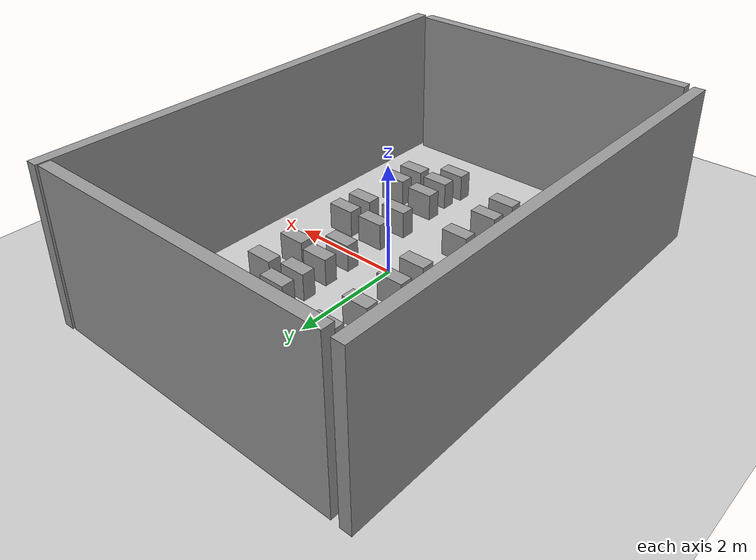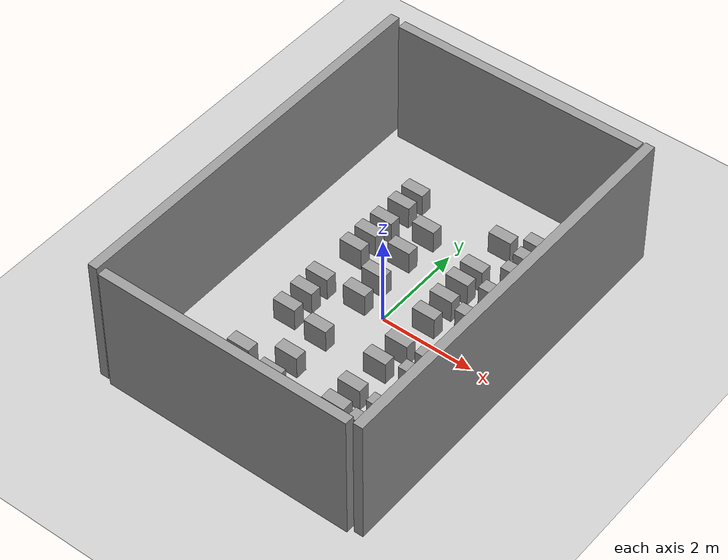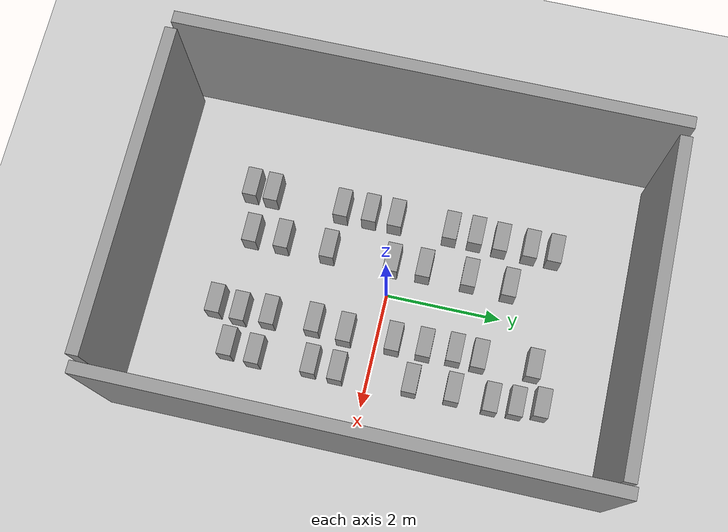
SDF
<sdf version="1.7">
 <world name="default">
  <light name="sun" type="directional">
   <pose>0 0 10 0 -0 0</pose>
   <diffuse>0.8 0.8 0.8 1</diffuse>
   <specular>0.2 0.2 0.2 1</specular>
   <attenuation>
    <range>1000</range>
    <constant>0.9</constant>
    <linear>0.01</linear>
    <quadratic>0.001</quadratic>
   </attenuation>
   <direction>-0.5 0.1 -0.9</direction>
   <spot><inner_angle>0</inner_angle><outer_angle>0</outer_angle><falloff>0</falloff></spot>
  </light>
  <model name="ground_plane">
   <static>1</static>
   <link name="link">
    <collision name="collision">
     <geometry><plane><normal>0 0 1</normal><size>100 100</size></plane></geometry>
     <surface>
      <contact><collide_bitmask>65535</collide_bitmask></contact>
      <friction><ode><mu>100</mu><mu2>50</mu2></ode></friction>
     </surface>
    </collision>
    <visual name="visual">
     <cast_shadows>0</cast_shadows>
     <geometry><plane><normal>0 0 1</normal><size>100 100</size></plane></geometry>
     <material>
      <script><uri>file://media/materials/scripts/gazebo.material</uri><name>Gazebo/Grey</name></script>
     </material>
    </visual>
   </link>
  </model>
  <gravity>0 0 -9.8</gravity>
  <magnetic_field>6e-06 2.3e-05 -4.2e-05</magnetic_field>
  <atmosphere type="adiabatic"/>
  <physics type="ode">
   <max_step_size>0.001</max_step_size>
   <real_time_factor>1</real_time_factor>
   <real_time_update_rate>1000</real_time_update_rate>
  </physics>
  <scene><ambient>0.4 0.4 0.4 1</ambient><background>0.7 0.7 0.7 1</background><shadows>1</shadows></scene>
  <spherical_coordinates>
   <surface_model>EARTH_WGS84</surface_model>
   <latitude_deg>0</latitude_deg>
   <longitude_deg>0</longitude_deg>
   <elevation>0</elevation>
   <heading_deg>0</heading_deg>
  </spherical_coordinates>
  <model name="grey_wall_8_5">
   <link name="link">
    <pose>0 4.29385 1.4 0 -0 0</pose>
    <inertial>
     <mass>1</mass>
     <inertia><ixx>1</ixx><ixy>0</ixy><ixz>0</ixz><iyy>1</iyy><iyz>0</iyz><izz>1</izz></inertia>
    </inertial>
    <visual name="visual">
     <cast_shadows>0</cast_shadows>
     <geometry><box><size>5.4 0.2 2.8</size></box></geometry>
     <material>
      <script>
       <uri>model://grey_wall/materials/scripts</uri>
       <uri>model://grey_wall/materials/textures</uri>
       <name>vrc/grey_wall</name>
      </script>
      <shader type="pixel"><normal_map>__default__</normal_map></shader>
      <ambient>1 1 1 1</ambient>
      <diffuse>1 1 1 1</diffuse>
      <specular>0 0 0 1</specular>
      <emissive>0 0 0 1</emissive>
     </material>
    </visual>
    <collision name="collision">
     <geometry><box><size>5.4 0.2 2.8</size></box></geometry>
     <surface>
      <friction>
       <ode><mu>1</mu><mu2>1</mu2><fdir1>0 0 0</fdir1><slip1>0</slip1><slip2>0</slip2></ode>
       <torsional>
        <coefficient>1</coefficient>
        <patch_radius>0</patch_radius>
        <surface_radius>0</surface_radius>
        <use_patch_radius>1</use_patch_radius>
        <ode><slip>0</slip></ode>
       </torsional>
      </friction>
      <bounce><restitution_coefficient>0</restitution_coefficient><threshold>1e+06</threshold></bounce>
      <contact>
       <collide_without_contact>0</collide_without_contact>
       <collide_without_contact_bitmask>1</collide_without_contact_bitmask>
       <collide_bitmask>1</collide_bitmask>
       <ode>
        <soft_cfm>0</soft_cfm>
        <soft_erp>0.2</soft_erp>
        <kp>1e+13</kp>
        <kd>1</kd>
        <max_vel>0.01</max_vel>
        <min_depth>0</min_depth>
       </ode>
       <bullet>
        <split_impulse>1</split_impulse>
        <split_impulse_penetration_threshold>-0.01</split_impulse_penetration_threshold>
        <soft_cfm>0</soft_cfm>
        <soft_erp>0.2</soft_erp>
        <kp>1e+13</kp>
        <kd>1</kd>
       </bullet>
      </contact>
     </surface>
    </collision>
   </link>
   <link name="link_clone">
    <pose>0.043634 12.556 1.4 0 -0 0</pose>
    <inertial>
     <mass>1</mass>
     <inertia><ixx>1</ixx><ixy>0</ixy><ixz>0</ixz><iyy>1</iyy><iyz>0</iyz><izz>1</izz></inertia>
    </inertial>
    <visual name="visual">
     <cast_shadows>0</cast_shadows>
     <geometry><box><size>5.4 0.2 2.8</size></box></geometry>
     <material>
      <script>
       <uri>model://grey_wall/materials/scripts</uri>
       <uri>model://grey_wall/materials/textures</uri>
       <name>vrc/grey_wall</name>
      </script>
      <shader type="pixel"><normal_map>__default__</normal_map></shader>
      <ambient>1 1 1 1</ambient>
      <diffuse>1 1 1 1</diffuse>
      <specular>0 0 0 1</specular>
      <emissive>0 0 0 1</emissive>
     </material>
    </visual>
    <collision name="collision">
     <geometry><box><size>5.4 0.2 2.8</size></box></geometry>
     <surface>
      <friction>
       <ode><mu>1</mu><mu2>1</mu2><fdir1>0 0 0</fdir1><slip1>0</slip1><slip2>0</slip2></ode>
       <torsional>
        <coefficient>1</coefficient>
        <patch_radius>0</patch_radius>
        <surface_radius>0</surface_radius>
        <use_patch_radius>1</use_patch_radius>
        <ode><slip>0</slip></ode>
       </torsional>
      </friction>
      <bounce><restitution_coefficient>0</restitution_coefficient><threshold>1e+06</threshold></bounce>
      <contact>
       <collide_without_contact>0</collide_without_contact>
       <collide_without_contact_bitmask>1</collide_without_contact_bitmask>
       <collide_bitmask>1</collide_bitmask>
       <ode>
        <soft_cfm>0</soft_cfm>
        <soft_erp>0.2</soft_erp>
        <kp>1e+13</kp>
        <kd>1</kd>
        <max_vel>0.01</max_vel>
        <min_depth>0</min_depth>
       </ode>
       <bullet>
        <split_impulse>1</split_impulse>
        <split_impulse_penetration_threshold>-0.01</split_impulse_penetration_threshold>
        <soft_cfm>0</soft_cfm>
        <soft_erp>0.2</soft_erp>
        <kp>1e+13</kp>
        <kd>1</kd>
       </bullet>
      </contact>
     </surface>
    </collision>
   </link>
   <link name="link_clone_0">
    <pose>2.87528 8.48137 1.4 0 -0 0</pose>
    <inertial>
     <mass>1</mass>
     <inertia><ixx>1</ixx><ixy>0</ixy><ixz>0</ixz><iyy>1</iyy><iyz>0</iyz><izz>1</izz></inertia>
    </inertial>
    <visual name="visual">
     <cast_shadows>0</cast_shadows>
     <geometry><box><size>0.2 8.4 2.8</size></box></geometry>
     <material>
      <script>
       <uri>model://grey_wall/materials/scripts</uri>
       <uri>model://grey_wall/materials/textures</uri>
       <name>vrc/grey_wall</name>
      </script>
      <shader type="pixel"><normal_map>__default__</normal_map></shader>
      <ambient>1 1 1 1</ambient>
      <diffuse>1 1 1 1</diffuse>
      <specular>0 0 0 1</specular>
      <emissive>0 0 0 1</emissive>
     </material>
    </visual>
    <collision name="collision">
     <geometry><box><size>0.2 8.4 2.8</size></box></geometry>
     <surface>
      <friction>
       <ode><mu>1</mu><mu2>1</mu2><fdir1>0 0 0</fdir1><slip1>0</slip1><slip2>0</slip2></ode>
       <torsional>
        <coefficient>1</coefficient>
        <patch_radius>0</patch_radius>
        <surface_radius>0</surface_radius>
        <use_patch_radius>1</use_patch_radius>
        <ode><slip>0</slip></ode>
       </torsional>
      </friction>
      <bounce><restitution_coefficient>0</restitution_coefficient><threshold>1e+06</threshold></bounce>
      <contact>
       <collide_without_contact>0</collide_without_contact>
       <collide_without_contact_bitmask>1</collide_without_contact_bitmask>
       <collide_bitmask>1</collide_bitmask>
       <ode>
        <soft_cfm>0</soft_cfm>
        <soft_erp>0.2</soft_erp>
        <kp>1e+13</kp>
        <kd>1</kd>
        <max_vel>0.01</max_vel>
        <min_depth>0</min_depth>
       </ode>
       <bullet>
        <split_impulse>1</split_impulse>
        <split_impulse_penetration_threshold>-0.01</split_impulse_penetration_threshold>
        <soft_cfm>0</soft_cfm>
        <soft_erp>0.2</soft_erp>
        <kp>1e+13</kp>
        <kd>1</kd>
       </bullet>
      </contact>
     </surface>
    </collision>
   </link>
   <link name="link_clone_0_clone">
    <pose>-2.90085 8.46581 1.4 0 -0 0</pose>
    <inertial>
     <mass>1</mass>
     <inertia><ixx>1</ixx><ixy>0</ixy><ixz>0</ixz><iyy>1</iyy><iyz>0</iyz><izz>1</izz></inertia>
    </inertial>
    <visual name="visual">
     <cast_shadows>0</cast_shadows>
     <geometry><box><size>0.2 8.4 2.8</size></box></geometry>
     <material>
      <script>
       <uri>model://grey_wall/materials/scripts</uri>
       <uri>model://grey_wall/materials/textures</uri>
       <name>vrc/grey_wall</name>
      </script>
      <shader type="pixel"><normal_map>__default__</normal_map></shader>
      <ambient>1 1 1 1</ambient>
      <diffuse>1 1 1 1</diffuse>
      <specular>0 0 0 1</specular>
      <emissive>0 0 0 1</emissive>
     </material>
    </visual>
    <collision name="collision">
     <geometry><box><size>0.2 8.4 2.8</size></box></geometry>
     <surface>
      <friction>
       <ode><mu>1</mu><mu2>1</mu2><fdir1>0 0 0</fdir1><slip1>0</slip1><slip2>0</slip2></ode>
       <torsional>
        <coefficient>1</coefficient>
        <patch_radius>0</patch_radius>
        <surface_radius>0</surface_radius>
        <use_patch_radius>1</use_patch_radius>
        <ode><slip>0</slip></ode>
       </torsional>
      </friction>
      <bounce><restitution_coefficient>0</restitution_coefficient><threshold>1e+06</threshold></bounce>
      <contact>
       <collide_without_contact>0</collide_without_contact>
       <collide_without_contact_bitmask>1</collide_without_contact_bitmask>
       <collide_bitmask>1</collide_bitmask>
       <ode>
        <soft_cfm>0</soft_cfm>
        <soft_erp>0.2</soft_erp>
        <kp>1e+13</kp>
        <kd>1</kd>
        <max_vel>0.01</max_vel>
        <min_depth>0</min_depth>
       </ode>
       <bullet>
        <split_impulse>1</split_impulse>
        <split_impulse_penetration_threshold>-0.01</split_impulse_penetration_threshold>
        <soft_cfm>0</soft_cfm>
        <soft_erp>0.2</soft_erp>
        <kp>1e+13</kp>
        <kd>1</kd>
       </bullet>
      </contact>
     </surface>
    </collision>
   </link>
   <static>1</static>
   <pose>-0.144395 -8.42706 0 0 -0 0</pose>
  </model>
  <model name="box_race_car_clone_20">
   <link name="link">
    <inertial>
     <mass>10</mass>
     <inertia>
      <ixx>0.260417</ixx>
      <ixy>0</ixy>
      <ixz>0</ixz>
      <iyy>0.416667</iyy>
      <iyz>0</iyz>
      <izz>0.260417</izz>
     </inertia>
    </inertial>
    <visual name="visual">
     <geometry><box><size>0.5 0.25 0.5</size></box></geometry>
     <material>
      <script><name>Gazebo/Grey</name><uri>file://media/materials/scripts/gazebo.material</uri></script>
      <shader type="pixel"><normal_map>__default__</normal_map></shader>
      <ambient>0.3 0.3 0.3 1</ambient>
      <diffuse>0.7 0.7 0.7 1</diffuse>
      <specular>0.01 0.01 0.01 1</specular>
      <emissive>0 0 0 1</emissive>
     </material>
    </visual>
    <collision name="collision">
     <geometry><box><size>0.5 0.25 0.5</size></box></geometry>
     <surface>
      <friction>
       <ode><mu>1</mu><mu2>1</mu2><fdir1>0 0 0</fdir1><slip1>0</slip1><slip2>0</slip2></ode>
       <torsional>
        <coefficient>1</coefficient>
        <patch_radius>0</patch_radius>
        <surface_radius>0</surface_radius>
        <use_patch_radius>1</use_patch_radius>
        <ode><slip>0</slip></ode>
       </torsional>
      </friction>
      <bounce><restitution_coefficient>0</restitution_coefficient><threshold>1e+06</threshold></bounce>
      <contact>
       <collide_without_contact>0</collide_without_contact>
       <collide_without_contact_bitmask>1</collide_without_contact_bitmask>
       <collide_bitmask>1</collide_bitmask>
       <ode>
        <soft_cfm>0</soft_cfm>
        <soft_erp>0.2</soft_erp>
        <kp>1e+13</kp>
        <kd>1</kd>
        <max_vel>0.01</max_vel>
        <min_depth>0</min_depth>
       </ode>
       <bullet>
        <split_impulse>1</split_impulse>
        <split_impulse_penetration_threshold>-0.01</split_impulse_penetration_threshold>
        <soft_cfm>0</soft_cfm>
        <soft_erp>0.2</soft_erp>
        <kp>1e+13</kp>
        <kd>1</kd>
       </bullet>
      </contact>
     </surface>
    </collision>
   </link>
   <static>0</static>
   <pose>-0.568656 -1.13771 0.25 0 -0 -2e-06</pose>
  </model>
  <model name="box_race_car_clone_20_clone">
   <link name="link">
    <inertial>
     <mass>10</mass>
     <inertia>
      <ixx>0.260417</ixx>
      <ixy>0</ixy>
      <ixz>0</ixz>
      <iyy>0.416667</iyy>
      <iyz>0</iyz>
      <izz>0.260417</izz>
     </inertia>
    </inertial>
    <visual name="visual">
     <geometry><box><size>0.5 0.25 0.5</size></box></geometry>
     <material>
      <script><name>Gazebo/Grey</name><uri>file://media/materials/scripts/gazebo.material</uri></script>
      <shader type="pixel"><normal_map>__default__</normal_map></shader>
      <ambient>0.3 0.3 0.3 1</ambient>
      <diffuse>0.7 0.7 0.7 1</diffuse>
      <specular>0.01 0.01 0.01 1</specular>
      <emissive>0 0 0 1</emissive>
     </material>
    </visual>
    <collision name="collision">
     <geometry><box><size>0.5 0.25 0.5</size></box></geometry>
     <surface>
      <friction>
       <ode><mu>1</mu><mu2>1</mu2><fdir1>0 0 0</fdir1><slip1>0</slip1><slip2>0</slip2></ode>
       <torsional>
        <coefficient>1</coefficient>
        <patch_radius>0</patch_radius>
        <surface_radius>0</surface_radius>
        <use_patch_radius>1</use_patch_radius>
        <ode><slip>0</slip></ode>
       </torsional>
      </friction>
      <bounce><restitution_coefficient>0</restitution_coefficient><threshold>1e+06</threshold></bounce>
      <contact>
       <collide_without_contact>0</collide_without_contact>
       <collide_without_contact_bitmask>1</collide_without_contact_bitmask>
       <collide_bitmask>1</collide_bitmask>
       <ode>
        <soft_cfm>0</soft_cfm>
        <soft_erp>0.2</soft_erp>
        <kp>1e+13</kp>
        <kd>1</kd>
        <max_vel>0.01</max_vel>
        <min_depth>0</min_depth>
       </ode>
       <bullet>
        <split_impulse>1</split_impulse>
        <split_impulse_penetration_threshold>-0.01</split_impulse_penetration_threshold>
        <soft_cfm>0</soft_cfm>
        <soft_erp>0.2</soft_erp>
        <kp>1e+13</kp>
        <kd>1</kd>
       </bullet>
      </contact>
     </surface>
    </collision>
   </link>
   <static>0</static>
   <pose>-0.571618 -1.9502 0.25 0 -0 -2e-06</pose>
  </model>
  <model name="box_race_car_clone_20_clone_0">
   <link name="link">
    <inertial>
     <mass>10</mass>
     <inertia>
      <ixx>0.260417</ixx>
      <ixy>0</ixy>
      <ixz>0</ixz>
      <iyy>0.416667</iyy>
      <iyz>0</iyz>
      <izz>0.260417</izz>
     </inertia>
    </inertial>
    <visual name="visual">
     <geometry><box><size>0.5 0.25 0.5</size></box></geometry>
     <material>
      <script><name>Gazebo/Grey</name><uri>file://media/materials/scripts/gazebo.material</uri></script>
      <shader type="pixel"><normal_map>__default__</normal_map></shader>
      <ambient>0.3 0.3 0.3 1</ambient>
      <diffuse>0.7 0.7 0.7 1</diffuse>
      <specular>0.01 0.01 0.01 1</specular>
      <emissive>0 0 0 1</emissive>
     </material>
    </visual>
    <collision name="collision">
     <geometry><box><size>0.5 0.25 0.5</size></box></geometry>
     <surface>
      <friction>
       <ode><mu>1</mu><mu2>1</mu2><fdir1>0 0 0</fdir1><slip1>0</slip1><slip2>0</slip2></ode>
       <torsional>
        <coefficient>1</coefficient>
        <patch_radius>0</patch_radius>
        <surface_radius>0</surface_radius>
        <use_patch_radius>1</use_patch_radius>
        <ode><slip>0</slip></ode>
       </torsional>
      </friction>
      <bounce><restitution_coefficient>0</restitution_coefficient><threshold>1e+06</threshold></bounce>
      <contact>
       <collide_without_contact>0</collide_without_contact>
       <collide_without_contact_bitmask>1</collide_without_contact_bitmask>
       <collide_bitmask>1</collide_bitmask>
       <ode>
        <soft_cfm>0</soft_cfm>
        <soft_erp>0.2</soft_erp>
        <kp>1e+13</kp>
        <kd>1</kd>
        <max_vel>0.01</max_vel>
        <min_depth>0</min_depth>
       </ode>
       <bullet>
        <split_impulse>1</split_impulse>
        <split_impulse_penetration_threshold>-0.01</split_impulse_penetration_threshold>
        <soft_cfm>0</soft_cfm>
        <soft_erp>0.2</soft_erp>
        <kp>1e+13</kp>
        <kd>1</kd>
       </bullet>
      </contact>
     </surface>
    </collision>
   </link>
   <static>0</static>
   <pose>-0.559718 -2.50311 0.25 0 -0 -2e-06</pose>
  </model>
  <model name="box_race_car_clone_20_clone_2">
   <link name="link">
    <inertial>
     <mass>10</mass>
     <inertia>
      <ixx>0.260417</ixx>
      <ixy>0</ixy>
      <ixz>0</ixz>
      <iyy>0.416667</iyy>
      <iyz>0</iyz>
      <izz>0.260417</izz>
     </inertia>
    </inertial>
    <visual name="visual">
     <geometry><box><size>0.5 0.25 0.5</size></box></geometry>
     <material>
      <script><name>Gazebo/Grey</name><uri>file://media/materials/scripts/gazebo.material</uri></script>
      <shader type="pixel"><normal_map>__default__</normal_map></shader>
      <ambient>0.3 0.3 0.3 1</ambient>
      <diffuse>0.7 0.7 0.7 1</diffuse>
      <specular>0.01 0.01 0.01 1</specular>
      <emissive>0 0 0 1</emissive>
     </material>
    </visual>
    <collision name="collision">
     <geometry><box><size>0.5 0.25 0.5</size></box></geometry>
     <surface>
      <friction>
       <ode><mu>1</mu><mu2>1</mu2><fdir1>0 0 0</fdir1><slip1>0</slip1><slip2>0</slip2></ode>
       <torsional>
        <coefficient>1</coefficient>
        <patch_radius>0</patch_radius>
        <surface_radius>0</surface_radius>
        <use_patch_radius>1</use_patch_radius>
        <ode><slip>0</slip></ode>
       </torsional>
      </friction>
      <bounce><restitution_coefficient>0</restitution_coefficient><threshold>1e+06</threshold></bounce>
      <contact>
       <collide_without_contact>0</collide_without_contact>
       <collide_without_contact_bitmask>1</collide_without_contact_bitmask>
       <collide_bitmask>1</collide_bitmask>
       <ode>
        <soft_cfm>0</soft_cfm>
        <soft_erp>0.2</soft_erp>
        <kp>1e+13</kp>
        <kd>1</kd>
        <max_vel>0.01</max_vel>
        <min_depth>0</min_depth>
       </ode>
       <bullet>
        <split_impulse>1</split_impulse>
        <split_impulse_penetration_threshold>-0.01</split_impulse_penetration_threshold>
        <soft_cfm>0</soft_cfm>
        <soft_erp>0.2</soft_erp>
        <kp>1e+13</kp>
        <kd>1</kd>
       </bullet>
      </contact>
     </surface>
    </collision>
   </link>
   <static>0</static>
   <pose>-0.568914 -0.016453 0.25 0 -0 -2e-06</pose>
  </model>
  <model name="box_race_car_clone_20_clone_3">
   <link name="link">
    <inertial>
     <mass>10</mass>
     <inertia>
      <ixx>0.260417</ixx>
      <ixy>0</ixy>
      <ixz>0</ixz>
      <iyy>0.416667</iyy>
      <iyz>0</iyz>
      <izz>0.260417</izz>
     </inertia>
    </inertial>
    <visual name="visual">
     <geometry><box><size>0.5 0.25 0.5</size></box></geometry>
     <material>
      <script><name>Gazebo/Grey</name><uri>file://media/materials/scripts/gazebo.material</uri></script>
      <shader type="pixel"><normal_map>__default__</normal_map></shader>
      <ambient>0.3 0.3 0.3 1</ambient>
      <diffuse>0.7 0.7 0.7 1</diffuse>
      <specular>0.01 0.01 0.01 1</specular>
      <emissive>0 0 0 1</emissive>
     </material>
    </visual>
    <collision name="collision">
     <geometry><box><size>0.5 0.25 0.5</size></box></geometry>
     <surface>
      <friction>
       <ode><mu>1</mu><mu2>1</mu2><fdir1>0 0 0</fdir1><slip1>0</slip1><slip2>0</slip2></ode>
       <torsional>
        <coefficient>1</coefficient>
        <patch_radius>0</patch_radius>
        <surface_radius>0</surface_radius>
        <use_patch_radius>1</use_patch_radius>
        <ode><slip>0</slip></ode>
       </torsional>
      </friction>
      <bounce><restitution_coefficient>0</restitution_coefficient><threshold>1e+06</threshold></bounce>
      <contact>
       <collide_without_contact>0</collide_without_contact>
       <collide_without_contact_bitmask>1</collide_without_contact_bitmask>
       <collide_bitmask>1</collide_bitmask>
       <ode>
        <soft_cfm>0</soft_cfm>
        <soft_erp>0.2</soft_erp>
        <kp>1e+13</kp>
        <kd>1</kd>
        <max_vel>0.01</max_vel>
        <min_depth>0</min_depth>
       </ode>
       <bullet>
        <split_impulse>1</split_impulse>
        <split_impulse_penetration_threshold>-0.01</split_impulse_penetration_threshold>
        <soft_cfm>0</soft_cfm>
        <soft_erp>0.2</soft_erp>
        <kp>1e+13</kp>
        <kd>1</kd>
       </bullet>
      </contact>
     </surface>
    </collision>
   </link>
   <static>0</static>
   <pose>-0.590353 0.546628 0.25 0 -0 -2e-06</pose>
  </model>
  <model name="box_race_car_clone_20_clone_4">
   <link name="link">
    <inertial>
     <mass>10</mass>
     <inertia>
      <ixx>0.260417</ixx>
      <ixy>0</ixy>
      <ixz>0</ixz>
      <iyy>0.416667</iyy>
      <iyz>0</iyz>
      <izz>0.260417</izz>
     </inertia>
    </inertial>
    <visual name="visual">
     <geometry><box><size>0.5 0.25 0.5</size></box></geometry>
     <material>
      <script><name>Gazebo/Grey</name><uri>file://media/materials/scripts/gazebo.material</uri></script>
      <shader type="pixel"><normal_map>__default__</normal_map></shader>
      <ambient>0.3 0.3 0.3 1</ambient>
      <diffuse>0.7 0.7 0.7 1</diffuse>
      <specular>0.01 0.01 0.01 1</specular>
      <emissive>0 0 0 1</emissive>
     </material>
    </visual>
    <collision name="collision">
     <geometry><box><size>0.5 0.25 0.5</size></box></geometry>
     <surface>
      <friction>
       <ode><mu>1</mu><mu2>1</mu2><fdir1>0 0 0</fdir1><slip1>0</slip1><slip2>0</slip2></ode>
       <torsional>
        <coefficient>1</coefficient>
        <patch_radius>0</patch_radius>
        <surface_radius>0</surface_radius>
        <use_patch_radius>1</use_patch_radius>
        <ode><slip>0</slip></ode>
       </torsional>
      </friction>
      <bounce><restitution_coefficient>0</restitution_coefficient><threshold>1e+06</threshold></bounce>
      <contact>
       <collide_without_contact>0</collide_without_contact>
       <collide_without_contact_bitmask>1</collide_without_contact_bitmask>
       <collide_bitmask>1</collide_bitmask>
       <ode>
        <soft_cfm>0</soft_cfm>
        <soft_erp>0.2</soft_erp>
        <kp>1e+13</kp>
        <kd>1</kd>
        <max_vel>0.01</max_vel>
        <min_depth>0</min_depth>
       </ode>
       <bullet>
        <split_impulse>1</split_impulse>
        <split_impulse_penetration_threshold>-0.01</split_impulse_penetration_threshold>
        <soft_cfm>0</soft_cfm>
        <soft_erp>0.2</soft_erp>
        <kp>1e+13</kp>
        <kd>1</kd>
       </bullet>
      </contact>
     </surface>
    </collision>
   </link>
   <static>0</static>
   <pose>-0.594673 1.33607 0.25 0 -0 -2e-06</pose>
  </model>
  <model name="box_race_car_clone_20_clone_5">
   <link name="link">
    <inertial>
     <mass>10</mass>
     <inertia>
      <ixx>0.260417</ixx>
      <ixy>0</ixy>
      <ixz>0</ixz>
      <iyy>0.416667</iyy>
      <iyz>0</iyz>
      <izz>0.260417</izz>
     </inertia>
    </inertial>
    <visual name="visual">
     <geometry><box><size>0.5 0.25 0.5</size></box></geometry>
     <material>
      <script><name>Gazebo/Grey</name><uri>file://media/materials/scripts/gazebo.material</uri></script>
      <shader type="pixel"><normal_map>__default__</normal_map></shader>
      <ambient>0.3 0.3 0.3 1</ambient>
      <diffuse>0.7 0.7 0.7 1</diffuse>
      <specular>0.01 0.01 0.01 1</specular>
      <emissive>0 0 0 1</emissive>
     </material>
    </visual>
    <collision name="collision">
     <geometry><box><size>0.5 0.25 0.5</size></box></geometry>
     <surface>
      <friction>
       <ode><mu>1</mu><mu2>1</mu2><fdir1>0 0 0</fdir1><slip1>0</slip1><slip2>0</slip2></ode>
       <torsional>
        <coefficient>1</coefficient>
        <patch_radius>0</patch_radius>
        <surface_radius>0</surface_radius>
        <use_patch_radius>1</use_patch_radius>
        <ode><slip>0</slip></ode>
       </torsional>
      </friction>
      <bounce><restitution_coefficient>0</restitution_coefficient><threshold>1e+06</threshold></bounce>
      <contact>
       <collide_without_contact>0</collide_without_contact>
       <collide_without_contact_bitmask>1</collide_without_contact_bitmask>
       <collide_bitmask>1</collide_bitmask>
       <ode>
        <soft_cfm>0</soft_cfm>
        <soft_erp>0.2</soft_erp>
        <kp>1e+13</kp>
        <kd>1</kd>
        <max_vel>0.01</max_vel>
        <min_depth>0</min_depth>
       </ode>
       <bullet>
        <split_impulse>1</split_impulse>
        <split_impulse_penetration_threshold>-0.01</split_impulse_penetration_threshold>
        <soft_cfm>0</soft_cfm>
        <soft_erp>0.2</soft_erp>
        <kp>1e+13</kp>
        <kd>1</kd>
       </bullet>
      </contact>
     </surface>
    </collision>
   </link>
   <static>0</static>
   <pose>-0.571957 2.04573 0.25 0 -0 -2e-06</pose>
  </model>
  <model name="box_race_car_clone_20_clone_7">
   <link name="link">
    <inertial>
     <mass>10</mass>
     <inertia>
      <ixx>0.260417</ixx>
      <ixy>0</ixy>
      <ixz>0</ixz>
      <iyy>0.416667</iyy>
      <iyz>0</iyz>
      <izz>0.260417</izz>
     </inertia>
    </inertial>
    <visual name="visual">
     <geometry><box><size>0.5 0.25 0.5</size></box></geometry>
     <material>
      <script><name>Gazebo/Grey</name><uri>file://media/materials/scripts/gazebo.material</uri></script>
      <shader type="pixel"><normal_map>__default__</normal_map></shader>
      <ambient>0.3 0.3 0.3 1</ambient>
      <diffuse>0.7 0.7 0.7 1</diffuse>
      <specular>0.01 0.01 0.01 1</specular>
      <emissive>0 0 0 1</emissive>
     </material>
    </visual>
    <collision name="collision">
     <geometry><box><size>0.5 0.25 0.5</size></box></geometry>
     <surface>
      <friction>
       <ode><mu>1</mu><mu2>1</mu2><fdir1>0 0 0</fdir1><slip1>0</slip1><slip2>0</slip2></ode>
       <torsional>
        <coefficient>1</coefficient>
        <patch_radius>0</patch_radius>
        <surface_radius>0</surface_radius>
        <use_patch_radius>1</use_patch_radius>
        <ode><slip>0</slip></ode>
       </torsional>
      </friction>
      <bounce><restitution_coefficient>0</restitution_coefficient><threshold>1e+06</threshold></bounce>
      <contact>
       <collide_without_contact>0</collide_without_contact>
       <collide_without_contact_bitmask>1</collide_without_contact_bitmask>
       <collide_bitmask>1</collide_bitmask>
       <ode>
        <soft_cfm>0</soft_cfm>
        <soft_erp>0.2</soft_erp>
        <kp>1e+13</kp>
        <kd>1</kd>
        <max_vel>0.01</max_vel>
        <min_depth>0</min_depth>
       </ode>
       <bullet>
        <split_impulse>1</split_impulse>
        <split_impulse_penetration_threshold>-0.01</split_impulse_penetration_threshold>
        <soft_cfm>0</soft_cfm>
        <soft_erp>0.2</soft_erp>
        <kp>1e+13</kp>
        <kd>1</kd>
       </bullet>
      </contact>
     </surface>
    </collision>
   </link>
   <static>0</static>
   <pose>-1.33065 2.69144 0.25 0 -0 -2e-06</pose>
  </model>
  <model name="box_race_car_clone_20_clone_8">
   <link name="link">
    <inertial>
     <mass>10</mass>
     <inertia>
      <ixx>0.260417</ixx>
      <ixy>0</ixy>
      <ixz>0</ixz>
      <iyy>0.416667</iyy>
      <iyz>0</iyz>
      <izz>0.260417</izz>
     </inertia>
    </inertial>
    <visual name="visual">
     <geometry><box><size>0.5 0.25 0.5</size></box></geometry>
     <material>
      <script><name>Gazebo/Grey</name><uri>file://media/materials/scripts/gazebo.material</uri></script>
      <shader type="pixel"><normal_map>__default__</normal_map></shader>
      <ambient>0.3 0.3 0.3 1</ambient>
      <diffuse>0.7 0.7 0.7 1</diffuse>
      <specular>0.01 0.01 0.01 1</specular>
      <emissive>0 0 0 1</emissive>
     </material>
    </visual>
    <collision name="collision">
     <geometry><box><size>0.5 0.25 0.5</size></box></geometry>
     <surface>
      <friction>
       <ode><mu>1</mu><mu2>1</mu2><fdir1>0 0 0</fdir1><slip1>0</slip1><slip2>0</slip2></ode>
       <torsional>
        <coefficient>1</coefficient>
        <patch_radius>0</patch_radius>
        <surface_radius>0</surface_radius>
        <use_patch_radius>1</use_patch_radius>
        <ode><slip>0</slip></ode>
       </torsional>
      </friction>
      <bounce><restitution_coefficient>0</restitution_coefficient><threshold>1e+06</threshold></bounce>
      <contact>
       <collide_without_contact>0</collide_without_contact>
       <collide_without_contact_bitmask>1</collide_without_contact_bitmask>
       <collide_bitmask>1</collide_bitmask>
       <ode>
        <soft_cfm>0</soft_cfm>
        <soft_erp>0.2</soft_erp>
        <kp>1e+13</kp>
        <kd>1</kd>
        <max_vel>0.01</max_vel>
        <min_depth>0</min_depth>
       </ode>
       <bullet>
        <split_impulse>1</split_impulse>
        <split_impulse_penetration_threshold>-0.01</split_impulse_penetration_threshold>
        <soft_cfm>0</soft_cfm>
        <soft_erp>0.2</soft_erp>
        <kp>1e+13</kp>
        <kd>1</kd>
       </bullet>
      </contact>
     </surface>
    </collision>
   </link>
   <static>0</static>
   <pose>-1.3245 2.26701 0.25 0 -0 -2e-06</pose>
  </model>
  <model name="box_race_car_clone_20_clone_9">
   <link name="link">
    <inertial>
     <mass>10</mass>
     <inertia>
      <ixx>0.260417</ixx>
      <ixy>0</ixy>
      <ixz>0</ixz>
      <iyy>0.416667</iyy>
      <iyz>0</iyz>
      <izz>0.260417</izz>
     </inertia>
    </inertial>
    <visual name="visual">
     <geometry><box><size>0.5 0.25 0.5</size></box></geometry>
     <material>
      <script><name>Gazebo/Grey</name><uri>file://media/materials/scripts/gazebo.material</uri></script>
      <shader type="pixel"><normal_map>__default__</normal_map></shader>
      <ambient>0.3 0.3 0.3 1</ambient>
      <diffuse>0.7 0.7 0.7 1</diffuse>
      <specular>0.01 0.01 0.01 1</specular>
      <emissive>0 0 0 1</emissive>
     </material>
    </visual>
    <collision name="collision">
     <geometry><box><size>0.5 0.25 0.5</size></box></geometry>
     <surface>
      <friction>
       <ode><mu>1</mu><mu2>1</mu2><fdir1>0 0 0</fdir1><slip1>0</slip1><slip2>0</slip2></ode>
       <torsional>
        <coefficient>1</coefficient>
        <patch_radius>0</patch_radius>
        <surface_radius>0</surface_radius>
        <use_patch_radius>1</use_patch_radius>
        <ode><slip>0</slip></ode>
       </torsional>
      </friction>
      <bounce><restitution_coefficient>0</restitution_coefficient><threshold>1e+06</threshold></bounce>
      <contact>
       <collide_without_contact>0</collide_without_contact>
       <collide_without_contact_bitmask>1</collide_without_contact_bitmask>
       <collide_bitmask>1</collide_bitmask>
       <ode>
        <soft_cfm>0</soft_cfm>
        <soft_erp>0.2</soft_erp>
        <kp>1e+13</kp>
        <kd>1</kd>
        <max_vel>0.01</max_vel>
        <min_depth>0</min_depth>
       </ode>
       <bullet>
        <split_impulse>1</split_impulse>
        <split_impulse_penetration_threshold>-0.01</split_impulse_penetration_threshold>
        <soft_cfm>0</soft_cfm>
        <soft_erp>0.2</soft_erp>
        <kp>1e+13</kp>
        <kd>1</kd>
       </bullet>
      </contact>
     </surface>
    </collision>
   </link>
   <static>0</static>
   <pose>-1.33137 1.74434 0.25 0 -0 -2e-06</pose>
  </model>
  <model name="box_race_car_clone_20_clone_10">
   <link name="link">
    <inertial>
     <mass>10</mass>
     <inertia>
      <ixx>0.260417</ixx>
      <ixy>0</ixy>
      <ixz>0</ixz>
      <iyy>0.416667</iyy>
      <iyz>0</iyz>
      <izz>0.260417</izz>
     </inertia>
    </inertial>
    <visual name="visual">
     <geometry><box><size>0.5 0.25 0.5</size></box></geometry>
     <material>
      <script><name>Gazebo/Grey</name><uri>file://media/materials/scripts/gazebo.material</uri></script>
      <shader type="pixel"><normal_map>__default__</normal_map></shader>
      <ambient>0.3 0.3 0.3 1</ambient>
      <diffuse>0.7 0.7 0.7 1</diffuse>
      <specular>0.01 0.01 0.01 1</specular>
      <emissive>0 0 0 1</emissive>
     </material>
    </visual>
    <collision name="collision">
     <geometry><box><size>0.5 0.25 0.5</size></box></geometry>
     <surface>
      <friction>
       <ode><mu>1</mu><mu2>1</mu2><fdir1>0 0 0</fdir1><slip1>0</slip1><slip2>0</slip2></ode>
       <torsional>
        <coefficient>1</coefficient>
        <patch_radius>0</patch_radius>
        <surface_radius>0</surface_radius>
        <use_patch_radius>1</use_patch_radius>
        <ode><slip>0</slip></ode>
       </torsional>
      </friction>
      <bounce><restitution_coefficient>0</restitution_coefficient><threshold>1e+06</threshold></bounce>
      <contact>
       <collide_without_contact>0</collide_without_contact>
       <collide_without_contact_bitmask>1</collide_without_contact_bitmask>
       <collide_bitmask>1</collide_bitmask>
       <ode>
        <soft_cfm>0</soft_cfm>
        <soft_erp>0.2</soft_erp>
        <kp>1e+13</kp>
        <kd>1</kd>
        <max_vel>0.01</max_vel>
        <min_depth>0</min_depth>
       </ode>
       <bullet>
        <split_impulse>1</split_impulse>
        <split_impulse_penetration_threshold>-0.01</split_impulse_penetration_threshold>
        <soft_cfm>0</soft_cfm>
        <soft_erp>0.2</soft_erp>
        <kp>1e+13</kp>
        <kd>1</kd>
       </bullet>
      </contact>
     </surface>
    </collision>
   </link>
   <static>0</static>
   <pose>-1.35542 1.30114 0.25 0 -0 -2e-06</pose>
  </model>
  <model name="box_race_car_clone_20_clone_11">
   <link name="link">
    <inertial>
     <mass>10</mass>
     <inertia>
      <ixx>0.260417</ixx>
      <ixy>0</ixy>
      <ixz>0</ixz>
      <iyy>0.416667</iyy>
      <iyz>0</iyz>
      <izz>0.260417</izz>
     </inertia>
    </inertial>
    <visual name="visual">
     <geometry><box><size>0.5 0.25 0.5</size></box></geometry>
     <material>
      <script><name>Gazebo/Grey</name><uri>file://media/materials/scripts/gazebo.material</uri></script>
      <shader type="pixel"><normal_map>__default__</normal_map></shader>
      <ambient>0.3 0.3 0.3 1</ambient>
      <diffuse>0.7 0.7 0.7 1</diffuse>
      <specular>0.01 0.01 0.01 1</specular>
      <emissive>0 0 0 1</emissive>
     </material>
    </visual>
    <collision name="collision">
     <geometry><box><size>0.5 0.25 0.5</size></box></geometry>
     <surface>
      <friction>
       <ode><mu>1</mu><mu2>1</mu2><fdir1>0 0 0</fdir1><slip1>0</slip1><slip2>0</slip2></ode>
       <torsional>
        <coefficient>1</coefficient>
        <patch_radius>0</patch_radius>
        <surface_radius>0</surface_radius>
        <use_patch_radius>1</use_patch_radius>
        <ode><slip>0</slip></ode>
       </torsional>
      </friction>
      <bounce><restitution_coefficient>0</restitution_coefficient><threshold>1e+06</threshold></bounce>
      <contact>
       <collide_without_contact>0</collide_without_contact>
       <collide_without_contact_bitmask>1</collide_without_contact_bitmask>
       <collide_bitmask>1</collide_bitmask>
       <ode>
        <soft_cfm>0</soft_cfm>
        <soft_erp>0.2</soft_erp>
        <kp>1e+13</kp>
        <kd>1</kd>
        <max_vel>0.01</max_vel>
        <min_depth>0</min_depth>
       </ode>
       <bullet>
        <split_impulse>1</split_impulse>
        <split_impulse_penetration_threshold>-0.01</split_impulse_penetration_threshold>
        <soft_cfm>0</soft_cfm>
        <soft_erp>0.2</soft_erp>
        <kp>1e+13</kp>
        <kd>1</kd>
       </bullet>
      </contact>
     </surface>
    </collision>
   </link>
   <static>0</static>
   <pose>-1.34991 0.856999 0.25 0 -0 -2e-06</pose>
  </model>
  <model name="box_race_car_clone_20_clone_12">
   <link name="link">
    <inertial>
     <mass>10</mass>
     <inertia>
      <ixx>0.260417</ixx>
      <ixy>0</ixy>
      <ixz>0</ixz>
      <iyy>0.416667</iyy>
      <iyz>0</iyz>
      <izz>0.260417</izz>
     </inertia>
    </inertial>
    <visual name="visual">
     <geometry><box><size>0.5 0.25 0.5</size></box></geometry>
     <material>
      <script><name>Gazebo/Grey</name><uri>file://media/materials/scripts/gazebo.material</uri></script>
      <shader type="pixel"><normal_map>__default__</normal_map></shader>
      <ambient>0.3 0.3 0.3 1</ambient>
      <diffuse>0.7 0.7 0.7 1</diffuse>
      <specular>0.01 0.01 0.01 1</specular>
      <emissive>0 0 0 1</emissive>
     </material>
    </visual>
    <collision name="collision">
     <geometry><box><size>0.5 0.25 0.5</size></box></geometry>
     <surface>
      <friction>
       <ode><mu>1</mu><mu2>1</mu2><fdir1>0 0 0</fdir1><slip1>0</slip1><slip2>0</slip2></ode>
       <torsional>
        <coefficient>1</coefficient>
        <patch_radius>0</patch_radius>
        <surface_radius>0</surface_radius>
        <use_patch_radius>1</use_patch_radius>
        <ode><slip>0</slip></ode>
       </torsional>
      </friction>
      <bounce><restitution_coefficient>0</restitution_coefficient><threshold>1e+06</threshold></bounce>
      <contact>
       <collide_without_contact>0</collide_without_contact>
       <collide_without_contact_bitmask>1</collide_without_contact_bitmask>
       <collide_bitmask>1</collide_bitmask>
       <ode>
        <soft_cfm>0</soft_cfm>
        <soft_erp>0.2</soft_erp>
        <kp>1e+13</kp>
        <kd>1</kd>
        <max_vel>0.01</max_vel>
        <min_depth>0</min_depth>
       </ode>
       <bullet>
        <split_impulse>1</split_impulse>
        <split_impulse_penetration_threshold>-0.01</split_impulse_penetration_threshold>
        <soft_cfm>0</soft_cfm>
        <soft_erp>0.2</soft_erp>
        <kp>1e+13</kp>
        <kd>1</kd>
       </bullet>
      </contact>
     </surface>
    </collision>
   </link>
   <static>0</static>
   <pose>-1.36143 -0.11935 0.25 0 -0 -2e-06</pose>
  </model>
  <model name="box_race_car_clone_20_clone_13">
   <link name="link">
    <inertial>
     <mass>10</mass>
     <inertia>
      <ixx>0.260417</ixx>
      <ixy>0</ixy>
      <ixz>0</ixz>
      <iyy>0.416667</iyy>
      <iyz>0</iyz>
      <izz>0.260417</izz>
     </inertia>
    </inertial>
    <visual name="visual">
     <geometry><box><size>0.5 0.25 0.5</size></box></geometry>
     <material>
      <script><name>Gazebo/Grey</name><uri>file://media/materials/scripts/gazebo.material</uri></script>
      <shader type="pixel"><normal_map>__default__</normal_map></shader>
      <ambient>0.3 0.3 0.3 1</ambient>
      <diffuse>0.7 0.7 0.7 1</diffuse>
      <specular>0.01 0.01 0.01 1</specular>
      <emissive>0 0 0 1</emissive>
     </material>
    </visual>
    <collision name="collision">
     <geometry><box><size>0.5 0.25 0.5</size></box></geometry>
     <surface>
      <friction>
       <ode><mu>1</mu><mu2>1</mu2><fdir1>0 0 0</fdir1><slip1>0</slip1><slip2>0</slip2></ode>
       <torsional>
        <coefficient>1</coefficient>
        <patch_radius>0</patch_radius>
        <surface_radius>0</surface_radius>
        <use_patch_radius>1</use_patch_radius>
        <ode><slip>0</slip></ode>
       </torsional>
      </friction>
      <bounce><restitution_coefficient>0</restitution_coefficient><threshold>1e+06</threshold></bounce>
      <contact>
       <collide_without_contact>0</collide_without_contact>
       <collide_without_contact_bitmask>1</collide_without_contact_bitmask>
       <collide_bitmask>1</collide_bitmask>
       <ode>
        <soft_cfm>0</soft_cfm>
        <soft_erp>0.2</soft_erp>
        <kp>1e+13</kp>
        <kd>1</kd>
        <max_vel>0.01</max_vel>
        <min_depth>0</min_depth>
       </ode>
       <bullet>
        <split_impulse>1</split_impulse>
        <split_impulse_penetration_threshold>-0.01</split_impulse_penetration_threshold>
        <soft_cfm>0</soft_cfm>
        <soft_erp>0.2</soft_erp>
        <kp>1e+13</kp>
        <kd>1</kd>
       </bullet>
      </contact>
     </surface>
    </collision>
   </link>
   <static>0</static>
   <pose>-1.35625 -0.573354 0.25 0 -0 -2e-06</pose>
  </model>
  <model name="box_race_car_clone_20_clone_14">
   <link name="link">
    <inertial>
     <mass>10</mass>
     <inertia>
      <ixx>0.260417</ixx>
      <ixy>0</ixy>
      <ixz>0</ixz>
      <iyy>0.416667</iyy>
      <iyz>0</iyz>
      <izz>0.260417</izz>
     </inertia>
    </inertial>
    <visual name="visual">
     <geometry><box><size>0.5 0.25 0.5</size></box></geometry>
     <material>
      <script><name>Gazebo/Grey</name><uri>file://media/materials/scripts/gazebo.material</uri></script>
      <shader type="pixel"><normal_map>__default__</normal_map></shader>
      <ambient>0.3 0.3 0.3 1</ambient>
      <diffuse>0.7 0.7 0.7 1</diffuse>
      <specular>0.01 0.01 0.01 1</specular>
      <emissive>0 0 0 1</emissive>
     </material>
    </visual>
    <collision name="collision">
     <geometry><box><size>0.5 0.25 0.5</size></box></geometry>
     <surface>
      <friction>
       <ode><mu>1</mu><mu2>1</mu2><fdir1>0 0 0</fdir1><slip1>0</slip1><slip2>0</slip2></ode>
       <torsional>
        <coefficient>1</coefficient>
        <patch_radius>0</patch_radius>
        <surface_radius>0</surface_radius>
        <use_patch_radius>1</use_patch_radius>
        <ode><slip>0</slip></ode>
       </torsional>
      </friction>
      <bounce><restitution_coefficient>0</restitution_coefficient><threshold>1e+06</threshold></bounce>
      <contact>
       <collide_without_contact>0</collide_without_contact>
       <collide_without_contact_bitmask>1</collide_without_contact_bitmask>
       <collide_bitmask>1</collide_bitmask>
       <ode>
        <soft_cfm>0</soft_cfm>
        <soft_erp>0.2</soft_erp>
        <kp>1e+13</kp>
        <kd>1</kd>
        <max_vel>0.01</max_vel>
        <min_depth>0</min_depth>
       </ode>
       <bullet>
        <split_impulse>1</split_impulse>
        <split_impulse_penetration_threshold>-0.01</split_impulse_penetration_threshold>
        <soft_cfm>0</soft_cfm>
        <soft_erp>0.2</soft_erp>
        <kp>1e+13</kp>
        <kd>1</kd>
       </bullet>
      </contact>
     </surface>
    </collision>
   </link>
   <static>0</static>
   <pose>-1.34277 -1.07695 0.25 0 -0 -2e-06</pose>
  </model>
  <model name="box_race_car_clone_20_clone_15">
   <link name="link">
    <inertial>
     <mass>10</mass>
     <inertia>
      <ixx>0.260417</ixx>
      <ixy>0</ixy>
      <ixz>0</ixz>
      <iyy>0.416667</iyy>
      <iyz>0</iyz>
      <izz>0.260417</izz>
     </inertia>
    </inertial>
    <visual name="visual">
     <geometry><box><size>0.5 0.25 0.5</size></box></geometry>
     <material>
      <script><name>Gazebo/Grey</name><uri>file://media/materials/scripts/gazebo.material</uri></script>
      <shader type="pixel"><normal_map>__default__</normal_map></shader>
      <ambient>0.3 0.3 0.3 1</ambient>
      <diffuse>0.7 0.7 0.7 1</diffuse>
      <specular>0.01 0.01 0.01 1</specular>
      <emissive>0 0 0 1</emissive>
     </material>
    </visual>
    <collision name="collision">
     <geometry><box><size>0.5 0.25 0.5</size></box></geometry>
     <surface>
      <friction>
       <ode><mu>1</mu><mu2>1</mu2><fdir1>0 0 0</fdir1><slip1>0</slip1><slip2>0</slip2></ode>
       <torsional>
        <coefficient>1</coefficient>
        <patch_radius>0</patch_radius>
        <surface_radius>0</surface_radius>
        <use_patch_radius>1</use_patch_radius>
        <ode><slip>0</slip></ode>
       </torsional>
      </friction>
      <bounce><restitution_coefficient>0</restitution_coefficient><threshold>1e+06</threshold></bounce>
      <contact>
       <collide_without_contact>0</collide_without_contact>
       <collide_without_contact_bitmask>1</collide_without_contact_bitmask>
       <collide_bitmask>1</collide_bitmask>
       <ode>
        <soft_cfm>0</soft_cfm>
        <soft_erp>0.2</soft_erp>
        <kp>1e+13</kp>
        <kd>1</kd>
        <max_vel>0.01</max_vel>
        <min_depth>0</min_depth>
       </ode>
       <bullet>
        <split_impulse>1</split_impulse>
        <split_impulse_penetration_threshold>-0.01</split_impulse_penetration_threshold>
        <soft_cfm>0</soft_cfm>
        <soft_erp>0.2</soft_erp>
        <kp>1e+13</kp>
        <kd>1</kd>
       </bullet>
      </contact>
     </surface>
    </collision>
   </link>
   <static>0</static>
   <pose>-1.36312 -2.32916 0.25 0 -0 -2e-06</pose>
  </model>
  <model name="box_race_car_clone_20_clone_16">
   <link name="link">
    <inertial>
     <mass>10</mass>
     <inertia>
      <ixx>0.260417</ixx>
      <ixy>0</ixy>
      <ixz>0</ixz>
      <iyy>0.416667</iyy>
      <iyz>0</iyz>
      <izz>0.260417</izz>
     </inertia>
    </inertial>
    <visual name="visual">
     <geometry><box><size>0.5 0.25 0.5</size></box></geometry>
     <material>
      <script><name>Gazebo/Grey</name><uri>file://media/materials/scripts/gazebo.material</uri></script>
      <shader type="pixel"><normal_map>__default__</normal_map></shader>
      <ambient>0.3 0.3 0.3 1</ambient>
      <diffuse>0.7 0.7 0.7 1</diffuse>
      <specular>0.01 0.01 0.01 1</specular>
      <emissive>0 0 0 1</emissive>
     </material>
    </visual>
    <collision name="collision">
     <geometry><box><size>0.5 0.25 0.5</size></box></geometry>
     <surface>
      <friction>
       <ode><mu>1</mu><mu2>1</mu2><fdir1>0 0 0</fdir1><slip1>0</slip1><slip2>0</slip2></ode>
       <torsional>
        <coefficient>1</coefficient>
        <patch_radius>0</patch_radius>
        <surface_radius>0</surface_radius>
        <use_patch_radius>1</use_patch_radius>
        <ode><slip>0</slip></ode>
       </torsional>
      </friction>
      <bounce><restitution_coefficient>0</restitution_coefficient><threshold>1e+06</threshold></bounce>
      <contact>
       <collide_without_contact>0</collide_without_contact>
       <collide_without_contact_bitmask>1</collide_without_contact_bitmask>
       <collide_bitmask>1</collide_bitmask>
       <ode>
        <soft_cfm>0</soft_cfm>
        <soft_erp>0.2</soft_erp>
        <kp>1e+13</kp>
        <kd>1</kd>
        <max_vel>0.01</max_vel>
        <min_depth>0</min_depth>
       </ode>
       <bullet>
        <split_impulse>1</split_impulse>
        <split_impulse_penetration_threshold>-0.01</split_impulse_penetration_threshold>
        <soft_cfm>0</soft_cfm>
        <soft_erp>0.2</soft_erp>
        <kp>1e+13</kp>
        <kd>1</kd>
       </bullet>
      </contact>
     </surface>
    </collision>
   </link>
   <static>0</static>
   <pose>-1.37511 -2.70369 0.25 0 -0 -2e-06</pose>
  </model>
  <model name="box_race_car_clone_20_clone_18">
   <link name="link">
    <inertial>
     <mass>10</mass>
     <inertia>
      <ixx>0.260417</ixx>
      <ixy>0</ixy>
      <ixz>0</ixz>
      <iyy>0.416667</iyy>
      <iyz>0</iyz>
      <izz>0.260417</izz>
     </inertia>
    </inertial>
    <visual name="visual">
     <geometry><box><size>0.5 0.25 0.5</size></box></geometry>
     <material>
      <script><name>Gazebo/Grey</name><uri>file://media/materials/scripts/gazebo.material</uri></script>
      <shader type="pixel"><normal_map>__default__</normal_map></shader>
      <ambient>0.3 0.3 0.3 1</ambient>
      <diffuse>0.7 0.7 0.7 1</diffuse>
      <specular>0.01 0.01 0.01 1</specular>
      <emissive>0 0 0 1</emissive>
     </material>
    </visual>
    <collision name="collision">
     <geometry><box><size>0.5 0.25 0.5</size></box></geometry>
     <surface>
      <friction>
       <ode><mu>1</mu><mu2>1</mu2><fdir1>0 0 0</fdir1><slip1>0</slip1><slip2>0</slip2></ode>
       <torsional>
        <coefficient>1</coefficient>
        <patch_radius>0</patch_radius>
        <surface_radius>0</surface_radius>
        <use_patch_radius>1</use_patch_radius>
        <ode><slip>0</slip></ode>
       </torsional>
      </friction>
      <bounce><restitution_coefficient>0</restitution_coefficient><threshold>1e+06</threshold></bounce>
      <contact>
       <collide_without_contact>0</collide_without_contact>
       <collide_without_contact_bitmask>1</collide_without_contact_bitmask>
       <collide_bitmask>1</collide_bitmask>
       <ode>
        <soft_cfm>0</soft_cfm>
        <soft_erp>0.2</soft_erp>
        <kp>1e+13</kp>
        <kd>1</kd>
        <max_vel>0.01</max_vel>
        <min_depth>0</min_depth>
       </ode>
       <bullet>
        <split_impulse>1</split_impulse>
        <split_impulse_penetration_threshold>-0.01</split_impulse_penetration_threshold>
        <soft_cfm>0</soft_cfm>
        <soft_erp>0.2</soft_erp>
        <kp>1e+13</kp>
        <kd>1</kd>
       </bullet>
      </contact>
     </surface>
    </collision>
   </link>
   <static>0</static>
   <pose>0.782478 -2.80274 0.25 0 -0 -2e-06</pose>
  </model>
  <model name="box_race_car_clone_20_clone_19">
   <link name="link">
    <inertial>
     <mass>10</mass>
     <inertia>
      <ixx>0.260417</ixx>
      <ixy>0</ixy>
      <ixz>0</ixz>
      <iyy>0.416667</iyy>
      <iyz>0</iyz>
      <izz>0.260417</izz>
     </inertia>
    </inertial>
    <visual name="visual">
     <geometry><box><size>0.5 0.25 0.5</size></box></geometry>
     <material>
      <script><name>Gazebo/Grey</name><uri>file://media/materials/scripts/gazebo.material</uri></script>
      <shader type="pixel"><normal_map>__default__</normal_map></shader>
      <ambient>0.3 0.3 0.3 1</ambient>
      <diffuse>0.7 0.7 0.7 1</diffuse>
      <specular>0.01 0.01 0.01 1</specular>
      <emissive>0 0 0 1</emissive>
     </material>
    </visual>
    <collision name="collision">
     <geometry><box><size>0.5 0.25 0.5</size></box></geometry>
     <surface>
      <friction>
       <ode><mu>1</mu><mu2>1</mu2><fdir1>0 0 0</fdir1><slip1>0</slip1><slip2>0</slip2></ode>
       <torsional>
        <coefficient>1</coefficient>
        <patch_radius>0</patch_radius>
        <surface_radius>0</surface_radius>
        <use_patch_radius>1</use_patch_radius>
        <ode><slip>0</slip></ode>
       </torsional>
      </friction>
      <bounce><restitution_coefficient>0</restitution_coefficient><threshold>1e+06</threshold></bounce>
      <contact>
       <collide_without_contact>0</collide_without_contact>
       <collide_without_contact_bitmask>1</collide_without_contact_bitmask>
       <collide_bitmask>1</collide_bitmask>
       <ode>
        <soft_cfm>0</soft_cfm>
        <soft_erp>0.2</soft_erp>
        <kp>1e+13</kp>
        <kd>1</kd>
        <max_vel>0.01</max_vel>
        <min_depth>0</min_depth>
       </ode>
       <bullet>
        <split_impulse>1</split_impulse>
        <split_impulse_penetration_threshold>-0.01</split_impulse_penetration_threshold>
        <soft_cfm>0</soft_cfm>
        <soft_erp>0.2</soft_erp>
        <kp>1e+13</kp>
        <kd>1</kd>
       </bullet>
      </contact>
     </surface>
    </collision>
   </link>
   <static>0</static>
   <pose>0.826256 -2.36012 0.25 0 -0 -2e-06</pose>
  </model>
  <model name="box_race_car_clone_20_clone_20">
   <link name="link">
    <inertial>
     <mass>10</mass>
     <inertia>
      <ixx>0.260417</ixx>
      <ixy>0</ixy>
      <ixz>0</ixz>
      <iyy>0.416667</iyy>
      <iyz>0</iyz>
      <izz>0.260417</izz>
     </inertia>
    </inertial>
    <visual name="visual">
     <geometry><box><size>0.5 0.25 0.5</size></box></geometry>
     <material>
      <script><name>Gazebo/Grey</name><uri>file://media/materials/scripts/gazebo.material</uri></script>
      <shader type="pixel"><normal_map>__default__</normal_map></shader>
      <ambient>0.3 0.3 0.3 1</ambient>
      <diffuse>0.7 0.7 0.7 1</diffuse>
      <specular>0.01 0.01 0.01 1</specular>
      <emissive>0 0 0 1</emissive>
     </material>
    </visual>
    <collision name="collision">
     <geometry><box><size>0.5 0.25 0.5</size></box></geometry>
     <surface>
      <friction>
       <ode><mu>1</mu><mu2>1</mu2><fdir1>0 0 0</fdir1><slip1>0</slip1><slip2>0</slip2></ode>
       <torsional>
        <coefficient>1</coefficient>
        <patch_radius>0</patch_radius>
        <surface_radius>0</surface_radius>
        <use_patch_radius>1</use_patch_radius>
        <ode><slip>0</slip></ode>
       </torsional>
      </friction>
      <bounce><restitution_coefficient>0</restitution_coefficient><threshold>1e+06</threshold></bounce>
      <contact>
       <collide_without_contact>0</collide_without_contact>
       <collide_without_contact_bitmask>1</collide_without_contact_bitmask>
       <collide_bitmask>1</collide_bitmask>
       <ode>
        <soft_cfm>0</soft_cfm>
        <soft_erp>0.2</soft_erp>
        <kp>1e+13</kp>
        <kd>1</kd>
        <max_vel>0.01</max_vel>
        <min_depth>0</min_depth>
       </ode>
       <bullet>
        <split_impulse>1</split_impulse>
        <split_impulse_penetration_threshold>-0.01</split_impulse_penetration_threshold>
        <soft_cfm>0</soft_cfm>
        <soft_erp>0.2</soft_erp>
        <kp>1e+13</kp>
        <kd>1</kd>
       </bullet>
      </contact>
     </surface>
    </collision>
   </link>
   <static>0</static>
   <pose>0.7832 -1.85548 0.25 0 -0 -2e-06</pose>
  </model>
  <model name="box_race_car_clone_20_clone_21">
   <link name="link">
    <inertial>
     <mass>10</mass>
     <inertia>
      <ixx>0.260417</ixx>
      <ixy>0</ixy>
      <ixz>0</ixz>
      <iyy>0.416667</iyy>
      <iyz>0</iyz>
      <izz>0.260417</izz>
     </inertia>
    </inertial>
    <visual name="visual">
     <geometry><box><size>0.5 0.25 0.5</size></box></geometry>
     <material>
      <script><name>Gazebo/Grey</name><uri>file://media/materials/scripts/gazebo.material</uri></script>
      <shader type="pixel"><normal_map>__default__</normal_map></shader>
      <ambient>0.3 0.3 0.3 1</ambient>
      <diffuse>0.7 0.7 0.7 1</diffuse>
      <specular>0.01 0.01 0.01 1</specular>
      <emissive>0 0 0 1</emissive>
     </material>
    </visual>
    <collision name="collision">
     <geometry><box><size>0.5 0.25 0.5</size></box></geometry>
     <surface>
      <friction>
       <ode><mu>1</mu><mu2>1</mu2><fdir1>0 0 0</fdir1><slip1>0</slip1><slip2>0</slip2></ode>
       <torsional>
        <coefficient>1</coefficient>
        <patch_radius>0</patch_radius>
        <surface_radius>0</surface_radius>
        <use_patch_radius>1</use_patch_radius>
        <ode><slip>0</slip></ode>
       </torsional>
      </friction>
      <bounce><restitution_coefficient>0</restitution_coefficient><threshold>1e+06</threshold></bounce>
      <contact>
       <collide_without_contact>0</collide_without_contact>
       <collide_without_contact_bitmask>1</collide_without_contact_bitmask>
       <collide_bitmask>1</collide_bitmask>
       <ode>
        <soft_cfm>0</soft_cfm>
        <soft_erp>0.2</soft_erp>
        <kp>1e+13</kp>
        <kd>1</kd>
        <max_vel>0.01</max_vel>
        <min_depth>0</min_depth>
       </ode>
       <bullet>
        <split_impulse>1</split_impulse>
        <split_impulse_penetration_threshold>-0.01</split_impulse_penetration_threshold>
        <soft_cfm>0</soft_cfm>
        <soft_erp>0.2</soft_erp>
        <kp>1e+13</kp>
        <kd>1</kd>
       </bullet>
      </contact>
     </surface>
    </collision>
   </link>
   <static>0</static>
   <pose>0.748668 -1.08471 0.25 0 -0 -2e-06</pose>
  </model>
  <model name="box_race_car_clone_20_clone_22">
   <link name="link">
    <inertial>
     <mass>10</mass>
     <inertia>
      <ixx>0.260417</ixx>
      <ixy>0</ixy>
      <ixz>0</ixz>
      <iyy>0.416667</iyy>
      <iyz>0</iyz>
      <izz>0.260417</izz>
     </inertia>
    </inertial>
    <visual name="visual">
     <geometry><box><size>0.5 0.25 0.5</size></box></geometry>
     <material>
      <script><name>Gazebo/Grey</name><uri>file://media/materials/scripts/gazebo.material</uri></script>
      <shader type="pixel"><normal_map>__default__</normal_map></shader>
      <ambient>0.3 0.3 0.3 1</ambient>
      <diffuse>0.7 0.7 0.7 1</diffuse>
      <specular>0.01 0.01 0.01 1</specular>
      <emissive>0 0 0 1</emissive>
     </material>
    </visual>
    <collision name="collision">
     <geometry><box><size>0.5 0.25 0.5</size></box></geometry>
     <surface>
      <friction>
       <ode><mu>1</mu><mu2>1</mu2><fdir1>0 0 0</fdir1><slip1>0</slip1><slip2>0</slip2></ode>
       <torsional>
        <coefficient>1</coefficient>
        <patch_radius>0</patch_radius>
        <surface_radius>0</surface_radius>
        <use_patch_radius>1</use_patch_radius>
        <ode><slip>0</slip></ode>
       </torsional>
      </friction>
      <bounce><restitution_coefficient>0</restitution_coefficient><threshold>1e+06</threshold></bounce>
      <contact>
       <collide_without_contact>0</collide_without_contact>
       <collide_without_contact_bitmask>1</collide_without_contact_bitmask>
       <collide_bitmask>1</collide_bitmask>
       <ode>
        <soft_cfm>0</soft_cfm>
        <soft_erp>0.2</soft_erp>
        <kp>1e+13</kp>
        <kd>1</kd>
        <max_vel>0.01</max_vel>
        <min_depth>0</min_depth>
       </ode>
       <bullet>
        <split_impulse>1</split_impulse>
        <split_impulse_penetration_threshold>-0.01</split_impulse_penetration_threshold>
        <soft_cfm>0</soft_cfm>
        <soft_erp>0.2</soft_erp>
        <kp>1e+13</kp>
        <kd>1</kd>
       </bullet>
      </contact>
     </surface>
    </collision>
   </link>
   <static>0</static>
   <pose>0.796226 -0.523789 0.25 0 -0 -2e-06</pose>
  </model>
  <model name="box_race_car_clone_20_clone_23">
   <link name="link">
    <inertial>
     <mass>10</mass>
     <inertia>
      <ixx>0.260417</ixx>
      <ixy>0</ixy>
      <ixz>0</ixz>
      <iyy>0.416667</iyy>
      <iyz>0</iyz>
      <izz>0.260417</izz>
     </inertia>
    </inertial>
    <visual name="visual">
     <geometry><box><size>0.5 0.25 0.5</size></box></geometry>
     <material>
      <script><name>Gazebo/Grey</name><uri>file://media/materials/scripts/gazebo.material</uri></script>
      <shader type="pixel"><normal_map>__default__</normal_map></shader>
      <ambient>0.3 0.3 0.3 1</ambient>
      <diffuse>0.7 0.7 0.7 1</diffuse>
      <specular>0.01 0.01 0.01 1</specular>
      <emissive>0 0 0 1</emissive>
     </material>
    </visual>
    <collision name="collision">
     <geometry><box><size>0.5 0.25 0.5</size></box></geometry>
     <surface>
      <friction>
       <ode><mu>1</mu><mu2>1</mu2><fdir1>0 0 0</fdir1><slip1>0</slip1><slip2>0</slip2></ode>
       <torsional>
        <coefficient>1</coefficient>
        <patch_radius>0</patch_radius>
        <surface_radius>0</surface_radius>
        <use_patch_radius>1</use_patch_radius>
        <ode><slip>0</slip></ode>
       </torsional>
      </friction>
      <bounce><restitution_coefficient>0</restitution_coefficient><threshold>1e+06</threshold></bounce>
      <contact>
       <collide_without_contact>0</collide_without_contact>
       <collide_without_contact_bitmask>1</collide_without_contact_bitmask>
       <collide_bitmask>1</collide_bitmask>
       <ode>
        <soft_cfm>0</soft_cfm>
        <soft_erp>0.2</soft_erp>
        <kp>1e+13</kp>
        <kd>1</kd>
        <max_vel>0.01</max_vel>
        <min_depth>0</min_depth>
       </ode>
       <bullet>
        <split_impulse>1</split_impulse>
        <split_impulse_penetration_threshold>-0.01</split_impulse_penetration_threshold>
        <soft_cfm>0</soft_cfm>
        <soft_erp>0.2</soft_erp>
        <kp>1e+13</kp>
        <kd>1</kd>
       </bullet>
      </contact>
     </surface>
    </collision>
   </link>
   <static>0</static>
   <pose>0.773447 0.305807 0.25 0 -0 -2e-06</pose>
  </model>
  <model name="box_race_car_clone_20_clone_24">
   <link name="link">
    <inertial>
     <mass>10</mass>
     <inertia>
      <ixx>0.260417</ixx>
      <ixy>0</ixy>
      <ixz>0</ixz>
      <iyy>0.416667</iyy>
      <iyz>0</iyz>
      <izz>0.260417</izz>
     </inertia>
    </inertial>
    <visual name="visual">
     <geometry><box><size>0.5 0.25 0.5</size></box></geometry>
     <material>
      <script><name>Gazebo/Grey</name><uri>file://media/materials/scripts/gazebo.material</uri></script>
      <shader type="pixel"><normal_map>__default__</normal_map></shader>
      <ambient>0.3 0.3 0.3 1</ambient>
      <diffuse>0.7 0.7 0.7 1</diffuse>
      <specular>0.01 0.01 0.01 1</specular>
      <emissive>0 0 0 1</emissive>
     </material>
    </visual>
    <collision name="collision">
     <geometry><box><size>0.5 0.25 0.5</size></box></geometry>
     <surface>
      <friction>
       <ode><mu>1</mu><mu2>1</mu2><fdir1>0 0 0</fdir1><slip1>0</slip1><slip2>0</slip2></ode>
       <torsional>
        <coefficient>1</coefficient>
        <patch_radius>0</patch_radius>
        <surface_radius>0</surface_radius>
        <use_patch_radius>1</use_patch_radius>
        <ode><slip>0</slip></ode>
       </torsional>
      </friction>
      <bounce><restitution_coefficient>0</restitution_coefficient><threshold>1e+06</threshold></bounce>
      <contact>
       <collide_without_contact>0</collide_without_contact>
       <collide_without_contact_bitmask>1</collide_without_contact_bitmask>
       <collide_bitmask>1</collide_bitmask>
       <ode>
        <soft_cfm>0</soft_cfm>
        <soft_erp>0.2</soft_erp>
        <kp>1e+13</kp>
        <kd>1</kd>
        <max_vel>0.01</max_vel>
        <min_depth>0</min_depth>
       </ode>
       <bullet>
        <split_impulse>1</split_impulse>
        <split_impulse_penetration_threshold>-0.01</split_impulse_penetration_threshold>
        <soft_cfm>0</soft_cfm>
        <soft_erp>0.2</soft_erp>
        <kp>1e+13</kp>
        <kd>1</kd>
       </bullet>
      </contact>
     </surface>
    </collision>
   </link>
   <static>0</static>
   <pose>0.760915 0.839054 0.25 0 -0 -2e-06</pose>
  </model>
  <model name="box_race_car_clone_20_clone_25">
   <link name="link">
    <inertial>
     <mass>10</mass>
     <inertia>
      <ixx>0.260417</ixx>
      <ixy>0</ixy>
      <ixz>0</ixz>
      <iyy>0.416667</iyy>
      <iyz>0</iyz>
      <izz>0.260417</izz>
     </inertia>
    </inertial>
    <visual name="visual">
     <geometry><box><size>0.5 0.25 0.5</size></box></geometry>
     <material>
      <script><name>Gazebo/Grey</name><uri>file://media/materials/scripts/gazebo.material</uri></script>
      <shader type="pixel"><normal_map>__default__</normal_map></shader>
      <ambient>0.3 0.3 0.3 1</ambient>
      <diffuse>0.7 0.7 0.7 1</diffuse>
      <specular>0.01 0.01 0.01 1</specular>
      <emissive>0 0 0 1</emissive>
     </material>
    </visual>
    <collision name="collision">
     <geometry><box><size>0.5 0.25 0.5</size></box></geometry>
     <surface>
      <friction>
       <ode><mu>1</mu><mu2>1</mu2><fdir1>0 0 0</fdir1><slip1>0</slip1><slip2>0</slip2></ode>
       <torsional>
        <coefficient>1</coefficient>
        <patch_radius>0</patch_radius>
        <surface_radius>0</surface_radius>
        <use_patch_radius>1</use_patch_radius>
        <ode><slip>0</slip></ode>
       </torsional>
      </friction>
      <bounce><restitution_coefficient>0</restitution_coefficient><threshold>1e+06</threshold></bounce>
      <contact>
       <collide_without_contact>0</collide_without_contact>
       <collide_without_contact_bitmask>1</collide_without_contact_bitmask>
       <collide_bitmask>1</collide_bitmask>
       <ode>
        <soft_cfm>0</soft_cfm>
        <soft_erp>0.2</soft_erp>
        <kp>1e+13</kp>
        <kd>1</kd>
        <max_vel>0.01</max_vel>
        <min_depth>0</min_depth>
       </ode>
       <bullet>
        <split_impulse>1</split_impulse>
        <split_impulse_penetration_threshold>-0.01</split_impulse_penetration_threshold>
        <soft_cfm>0</soft_cfm>
        <soft_erp>0.2</soft_erp>
        <kp>1e+13</kp>
        <kd>1</kd>
       </bullet>
      </contact>
     </surface>
    </collision>
   </link>
   <static>0</static>
   <pose>0.737894 1.3529 0.25 0 -0 -2e-06</pose>
  </model>
  <model name="box_race_car_clone_20_clone_26">
   <link name="link">
    <inertial>
     <mass>10</mass>
     <inertia>
      <ixx>0.260417</ixx>
      <ixy>0</ixy>
      <ixz>0</ixz>
      <iyy>0.416667</iyy>
      <iyz>0</iyz>
      <izz>0.260417</izz>
     </inertia>
    </inertial>
    <visual name="visual">
     <geometry><box><size>0.5 0.25 0.5</size></box></geometry>
     <material>
      <script><name>Gazebo/Grey</name><uri>file://media/materials/scripts/gazebo.material</uri></script>
      <shader type="pixel"><normal_map>__default__</normal_map></shader>
      <ambient>0.3 0.3 0.3 1</ambient>
      <diffuse>0.7 0.7 0.7 1</diffuse>
      <specular>0.01 0.01 0.01 1</specular>
      <emissive>0 0 0 1</emissive>
     </material>
    </visual>
    <collision name="collision">
     <geometry><box><size>0.5 0.25 0.5</size></box></geometry>
     <surface>
      <friction>
       <ode><mu>1</mu><mu2>1</mu2><fdir1>0 0 0</fdir1><slip1>0</slip1><slip2>0</slip2></ode>
       <torsional>
        <coefficient>1</coefficient>
        <patch_radius>0</patch_radius>
        <surface_radius>0</surface_radius>
        <use_patch_radius>1</use_patch_radius>
        <ode><slip>0</slip></ode>
       </torsional>
      </friction>
      <bounce><restitution_coefficient>0</restitution_coefficient><threshold>1e+06</threshold></bounce>
      <contact>
       <collide_without_contact>0</collide_without_contact>
       <collide_without_contact_bitmask>1</collide_without_contact_bitmask>
       <collide_bitmask>1</collide_bitmask>
       <ode>
        <soft_cfm>0</soft_cfm>
        <soft_erp>0.2</soft_erp>
        <kp>1e+13</kp>
        <kd>1</kd>
        <max_vel>0.01</max_vel>
        <min_depth>0</min_depth>
       </ode>
       <bullet>
        <split_impulse>1</split_impulse>
        <split_impulse_penetration_threshold>-0.01</split_impulse_penetration_threshold>
        <soft_cfm>0</soft_cfm>
        <soft_erp>0.2</soft_erp>
        <kp>1e+13</kp>
        <kd>1</kd>
       </bullet>
      </contact>
     </surface>
    </collision>
   </link>
   <static>0</static>
   <pose>0.751464 1.77676 0.25 0 -0 -2e-06</pose>
  </model>
  <model name="box_race_car_clone_20_clone_27">
   <link name="link">
    <inertial>
     <mass>10</mass>
     <inertia>
      <ixx>0.260417</ixx>
      <ixy>0</ixy>
      <ixz>0</ixz>
      <iyy>0.416667</iyy>
      <iyz>0</iyz>
      <izz>0.260417</izz>
     </inertia>
    </inertial>
    <visual name="visual">
     <geometry><box><size>0.5 0.25 0.5</size></box></geometry>
     <material>
      <script><name>Gazebo/Grey</name><uri>file://media/materials/scripts/gazebo.material</uri></script>
      <shader type="pixel"><normal_map>__default__</normal_map></shader>
      <ambient>0.3 0.3 0.3 1</ambient>
      <diffuse>0.7 0.7 0.7 1</diffuse>
      <specular>0.01 0.01 0.01 1</specular>
      <emissive>0 0 0 1</emissive>
     </material>
    </visual>
    <collision name="collision">
     <geometry><box><size>0.5 0.25 0.5</size></box></geometry>
     <surface>
      <friction>
       <ode><mu>1</mu><mu2>1</mu2><fdir1>0 0 0</fdir1><slip1>0</slip1><slip2>0</slip2></ode>
       <torsional>
        <coefficient>1</coefficient>
        <patch_radius>0</patch_radius>
        <surface_radius>0</surface_radius>
        <use_patch_radius>1</use_patch_radius>
        <ode><slip>0</slip></ode>
       </torsional>
      </friction>
      <bounce><restitution_coefficient>0</restitution_coefficient><threshold>1e+06</threshold></bounce>
      <contact>
       <collide_without_contact>0</collide_without_contact>
       <collide_without_contact_bitmask>1</collide_without_contact_bitmask>
       <collide_bitmask>1</collide_bitmask>
       <ode>
        <soft_cfm>0</soft_cfm>
        <soft_erp>0.2</soft_erp>
        <kp>1e+13</kp>
        <kd>1</kd>
        <max_vel>0.01</max_vel>
        <min_depth>0</min_depth>
       </ode>
       <bullet>
        <split_impulse>1</split_impulse>
        <split_impulse_penetration_threshold>-0.01</split_impulse_penetration_threshold>
        <soft_cfm>0</soft_cfm>
        <soft_erp>0.2</soft_erp>
        <kp>1e+13</kp>
        <kd>1</kd>
       </bullet>
      </contact>
     </surface>
    </collision>
   </link>
   <static>0</static>
   <pose>0.712119 2.70554 0.25 0 -0 -2e-06</pose>
  </model>
  <model name="box_race_car_clone_20_clone_29">
   <link name="link">
    <inertial>
     <mass>10</mass>
     <inertia>
      <ixx>0.260417</ixx>
      <ixy>0</ixy>
      <ixz>0</ixz>
      <iyy>0.416667</iyy>
      <iyz>0</iyz>
      <izz>0.260417</izz>
     </inertia>
    </inertial>
    <visual name="visual">
     <geometry><box><size>0.5 0.25 0.5</size></box></geometry>
     <material>
      <script><name>Gazebo/Grey</name><uri>file://media/materials/scripts/gazebo.material</uri></script>
      <shader type="pixel"><normal_map>__default__</normal_map></shader>
      <ambient>0.3 0.3 0.3 1</ambient>
      <diffuse>0.7 0.7 0.7 1</diffuse>
      <specular>0.01 0.01 0.01 1</specular>
      <emissive>0 0 0 1</emissive>
     </material>
    </visual>
    <collision name="collision">
     <geometry><box><size>0.5 0.25 0.5</size></box></geometry>
     <surface>
      <friction>
       <ode><mu>1</mu><mu2>1</mu2><fdir1>0 0 0</fdir1><slip1>0</slip1><slip2>0</slip2></ode>
       <torsional>
        <coefficient>1</coefficient>
        <patch_radius>0</patch_radius>
        <surface_radius>0</surface_radius>
        <use_patch_radius>1</use_patch_radius>
        <ode><slip>0</slip></ode>
       </torsional>
      </friction>
      <bounce><restitution_coefficient>0</restitution_coefficient><threshold>1e+06</threshold></bounce>
      <contact>
       <collide_without_contact>0</collide_without_contact>
       <collide_without_contact_bitmask>1</collide_without_contact_bitmask>
       <collide_bitmask>1</collide_bitmask>
       <ode>
        <soft_cfm>0</soft_cfm>
        <soft_erp>0.2</soft_erp>
        <kp>1e+13</kp>
        <kd>1</kd>
        <max_vel>0.01</max_vel>
        <min_depth>0</min_depth>
       </ode>
       <bullet>
        <split_impulse>1</split_impulse>
        <split_impulse_penetration_threshold>-0.01</split_impulse_penetration_threshold>
        <soft_cfm>0</soft_cfm>
        <soft_erp>0.2</soft_erp>
        <kp>1e+13</kp>
        <kd>1</kd>
       </bullet>
      </contact>
     </surface>
    </collision>
   </link>
   <static>0</static>
   <pose>1.33184 2.95224 0.25 0 -0 -2e-06</pose>
  </model>
  <model name="box_race_car_clone_20_clone_30">
   <link name="link">
    <inertial>
     <mass>10</mass>
     <inertia>
      <ixx>0.260417</ixx>
      <ixy>0</ixy>
      <ixz>0</ixz>
      <iyy>0.416667</iyy>
      <iyz>0</iyz>
      <izz>0.260417</izz>
     </inertia>
    </inertial>
    <visual name="visual">
     <geometry><box><size>0.5 0.25 0.5</size></box></geometry>
     <material>
      <script><name>Gazebo/Grey</name><uri>file://media/materials/scripts/gazebo.material</uri></script>
      <shader type="pixel"><normal_map>__default__</normal_map></shader>
      <ambient>0.3 0.3 0.3 1</ambient>
      <diffuse>0.7 0.7 0.7 1</diffuse>
      <specular>0.01 0.01 0.01 1</specular>
      <emissive>0 0 0 1</emissive>
     </material>
    </visual>
    <collision name="collision">
     <geometry><box><size>0.5 0.25 0.5</size></box></geometry>
     <surface>
      <friction>
       <ode><mu>1</mu><mu2>1</mu2><fdir1>0 0 0</fdir1><slip1>0</slip1><slip2>0</slip2></ode>
       <torsional>
        <coefficient>1</coefficient>
        <patch_radius>0</patch_radius>
        <surface_radius>0</surface_radius>
        <use_patch_radius>1</use_patch_radius>
        <ode><slip>0</slip></ode>
       </torsional>
      </friction>
      <bounce><restitution_coefficient>0</restitution_coefficient><threshold>1e+06</threshold></bounce>
      <contact>
       <collide_without_contact>0</collide_without_contact>
       <collide_without_contact_bitmask>1</collide_without_contact_bitmask>
       <collide_bitmask>1</collide_bitmask>
       <ode>
        <soft_cfm>0</soft_cfm>
        <soft_erp>0.2</soft_erp>
        <kp>1e+13</kp>
        <kd>1</kd>
        <max_vel>0.01</max_vel>
        <min_depth>0</min_depth>
       </ode>
       <bullet>
        <split_impulse>1</split_impulse>
        <split_impulse_penetration_threshold>-0.01</split_impulse_penetration_threshold>
        <soft_cfm>0</soft_cfm>
        <soft_erp>0.2</soft_erp>
        <kp>1e+13</kp>
        <kd>1</kd>
       </bullet>
      </contact>
     </surface>
    </collision>
   </link>
   <static>0</static>
   <pose>1.39747 2.53575 0.25 0 -0 -2e-06</pose>
  </model>
  <model name="box_race_car_clone_20_clone_31">
   <link name="link">
    <inertial>
     <mass>10</mass>
     <inertia>
      <ixx>0.260417</ixx>
      <ixy>0</ixy>
      <ixz>0</ixz>
      <iyy>0.416667</iyy>
      <iyz>0</iyz>
      <izz>0.260417</izz>
     </inertia>
    </inertial>
    <visual name="visual">
     <geometry><box><size>0.5 0.25 0.5</size></box></geometry>
     <material>
      <script><name>Gazebo/Grey</name><uri>file://media/materials/scripts/gazebo.material</uri></script>
      <shader type="pixel"><normal_map>__default__</normal_map></shader>
      <ambient>0.3 0.3 0.3 1</ambient>
      <diffuse>0.7 0.7 0.7 1</diffuse>
      <specular>0.01 0.01 0.01 1</specular>
      <emissive>0 0 0 1</emissive>
     </material>
    </visual>
    <collision name="collision">
     <geometry><box><size>0.5 0.25 0.5</size></box></geometry>
     <surface>
      <friction>
       <ode><mu>1</mu><mu2>1</mu2><fdir1>0 0 0</fdir1><slip1>0</slip1><slip2>0</slip2></ode>
       <torsional>
        <coefficient>1</coefficient>
        <patch_radius>0</patch_radius>
        <surface_radius>0</surface_radius>
        <use_patch_radius>1</use_patch_radius>
        <ode><slip>0</slip></ode>
       </torsional>
      </friction>
      <bounce><restitution_coefficient>0</restitution_coefficient><threshold>1e+06</threshold></bounce>
      <contact>
       <collide_without_contact>0</collide_without_contact>
       <collide_without_contact_bitmask>1</collide_without_contact_bitmask>
       <collide_bitmask>1</collide_bitmask>
       <ode>
        <soft_cfm>0</soft_cfm>
        <soft_erp>0.2</soft_erp>
        <kp>1e+13</kp>
        <kd>1</kd>
        <max_vel>0.01</max_vel>
        <min_depth>0</min_depth>
       </ode>
       <bullet>
        <split_impulse>1</split_impulse>
        <split_impulse_penetration_threshold>-0.01</split_impulse_penetration_threshold>
        <soft_cfm>0</soft_cfm>
        <soft_erp>0.2</soft_erp>
        <kp>1e+13</kp>
        <kd>1</kd>
       </bullet>
      </contact>
     </surface>
    </collision>
   </link>
   <static>0</static>
   <pose>1.42333 2.1106 0.25 0 -0 -2e-06</pose>
  </model>
  <model name="box_race_car_clone_20_clone_32">
   <link name="link">
    <inertial>
     <mass>10</mass>
     <inertia>
      <ixx>0.260417</ixx>
      <ixy>0</ixy>
      <ixz>0</ixz>
      <iyy>0.416667</iyy>
      <iyz>0</iyz>
      <izz>0.260417</izz>
     </inertia>
    </inertial>
    <visual name="visual">
     <geometry><box><size>0.5 0.25 0.5</size></box></geometry>
     <material>
      <script><name>Gazebo/Grey</name><uri>file://media/materials/scripts/gazebo.material</uri></script>
      <shader type="pixel"><normal_map>__default__</normal_map></shader>
      <ambient>0.3 0.3 0.3 1</ambient>
      <diffuse>0.7 0.7 0.7 1</diffuse>
      <specular>0.01 0.01 0.01 1</specular>
      <emissive>0 0 0 1</emissive>
     </material>
    </visual>
    <collision name="collision">
     <geometry><box><size>0.5 0.25 0.5</size></box></geometry>
     <surface>
      <friction>
       <ode><mu>1</mu><mu2>1</mu2><fdir1>0 0 0</fdir1><slip1>0</slip1><slip2>0</slip2></ode>
       <torsional>
        <coefficient>1</coefficient>
        <patch_radius>0</patch_radius>
        <surface_radius>0</surface_radius>
        <use_patch_radius>1</use_patch_radius>
        <ode><slip>0</slip></ode>
       </torsional>
      </friction>
      <bounce><restitution_coefficient>0</restitution_coefficient><threshold>1e+06</threshold></bounce>
      <contact>
       <collide_without_contact>0</collide_without_contact>
       <collide_without_contact_bitmask>1</collide_without_contact_bitmask>
       <collide_bitmask>1</collide_bitmask>
       <ode>
        <soft_cfm>0</soft_cfm>
        <soft_erp>0.2</soft_erp>
        <kp>1e+13</kp>
        <kd>1</kd>
        <max_vel>0.01</max_vel>
        <min_depth>0</min_depth>
       </ode>
       <bullet>
        <split_impulse>1</split_impulse>
        <split_impulse_penetration_threshold>-0.01</split_impulse_penetration_threshold>
        <soft_cfm>0</soft_cfm>
        <soft_erp>0.2</soft_erp>
        <kp>1e+13</kp>
        <kd>1</kd>
       </bullet>
      </contact>
     </surface>
    </collision>
   </link>
   <static>0</static>
   <pose>1.4025 1.46001 0.25 0 -0 -2e-06</pose>
  </model>
  <model name="box_race_car_clone_20_clone_33">
   <link name="link">
    <inertial>
     <mass>10</mass>
     <inertia>
      <ixx>0.260417</ixx>
      <ixy>0</ixy>
      <ixz>0</ixz>
      <iyy>0.416667</iyy>
      <iyz>0</iyz>
      <izz>0.260417</izz>
     </inertia>
    </inertial>
    <visual name="visual">
     <geometry><box><size>0.5 0.25 0.5</size></box></geometry>
     <material>
      <script><name>Gazebo/Grey</name><uri>file://media/materials/scripts/gazebo.material</uri></script>
      <shader type="pixel"><normal_map>__default__</normal_map></shader>
      <ambient>0.3 0.3 0.3 1</ambient>
      <diffuse>0.7 0.7 0.7 1</diffuse>
      <specular>0.01 0.01 0.01 1</specular>
      <emissive>0 0 0 1</emissive>
     </material>
    </visual>
    <collision name="collision">
     <geometry><box><size>0.5 0.25 0.5</size></box></geometry>
     <surface>
      <friction>
       <ode><mu>1</mu><mu2>1</mu2><fdir1>0 0 0</fdir1><slip1>0</slip1><slip2>0</slip2></ode>
       <torsional>
        <coefficient>1</coefficient>
        <patch_radius>0</patch_radius>
        <surface_radius>0</surface_radius>
        <use_patch_radius>1</use_patch_radius>
        <ode><slip>0</slip></ode>
       </torsional>
      </friction>
      <bounce><restitution_coefficient>0</restitution_coefficient><threshold>1e+06</threshold></bounce>
      <contact>
       <collide_without_contact>0</collide_without_contact>
       <collide_without_contact_bitmask>1</collide_without_contact_bitmask>
       <collide_bitmask>1</collide_bitmask>
       <ode>
        <soft_cfm>0</soft_cfm>
        <soft_erp>0.2</soft_erp>
        <kp>1e+13</kp>
        <kd>1</kd>
        <max_vel>0.01</max_vel>
        <min_depth>0</min_depth>
       </ode>
       <bullet>
        <split_impulse>1</split_impulse>
        <split_impulse_penetration_threshold>-0.01</split_impulse_penetration_threshold>
        <soft_cfm>0</soft_cfm>
        <soft_erp>0.2</soft_erp>
        <kp>1e+13</kp>
        <kd>1</kd>
       </bullet>
      </contact>
     </surface>
    </collision>
   </link>
   <static>0</static>
   <pose>1.40903 0.739252 0.25 0 -0 -2e-06</pose>
  </model>
  <model name="box_race_car_clone_20_clone_34">
   <link name="link">
    <inertial>
     <mass>10</mass>
     <inertia>
      <ixx>0.260417</ixx>
      <ixy>0</ixy>
      <ixz>0</ixz>
      <iyy>0.416667</iyy>
      <iyz>0</iyz>
      <izz>0.260417</izz>
     </inertia>
    </inertial>
    <visual name="visual">
     <geometry><box><size>0.5 0.25 0.5</size></box></geometry>
     <material>
      <script><name>Gazebo/Grey</name><uri>file://media/materials/scripts/gazebo.material</uri></script>
      <shader type="pixel"><normal_map>__default__</normal_map></shader>
      <ambient>0.3 0.3 0.3 1</ambient>
      <diffuse>0.7 0.7 0.7 1</diffuse>
      <specular>0.01 0.01 0.01 1</specular>
      <emissive>0 0 0 1</emissive>
     </material>
    </visual>
    <collision name="collision">
     <geometry><box><size>0.5 0.25 0.5</size></box></geometry>
     <surface>
      <friction>
       <ode><mu>1</mu><mu2>1</mu2><fdir1>0 0 0</fdir1><slip1>0</slip1><slip2>0</slip2></ode>
       <torsional>
        <coefficient>1</coefficient>
        <patch_radius>0</patch_radius>
        <surface_radius>0</surface_radius>
        <use_patch_radius>1</use_patch_radius>
        <ode><slip>0</slip></ode>
       </torsional>
      </friction>
      <bounce><restitution_coefficient>0</restitution_coefficient><threshold>1e+06</threshold></bounce>
      <contact>
       <collide_without_contact>0</collide_without_contact>
       <collide_without_contact_bitmask>1</collide_without_contact_bitmask>
       <collide_bitmask>1</collide_bitmask>
       <ode>
        <soft_cfm>0</soft_cfm>
        <soft_erp>0.2</soft_erp>
        <kp>1e+13</kp>
        <kd>1</kd>
        <max_vel>0.01</max_vel>
        <min_depth>0</min_depth>
       </ode>
       <bullet>
        <split_impulse>1</split_impulse>
        <split_impulse_penetration_threshold>-0.01</split_impulse_penetration_threshold>
        <soft_cfm>0</soft_cfm>
        <soft_erp>0.2</soft_erp>
        <kp>1e+13</kp>
        <kd>1</kd>
       </bullet>
      </contact>
     </surface>
    </collision>
   </link>
   <static>0</static>
   <pose>1.46767 -0.51609 0.25 0 -0 -2e-06</pose>
  </model>
  <model name="box_race_car_clone_20_clone_35">
   <link name="link">
    <inertial>
     <mass>10</mass>
     <inertia>
      <ixx>0.260417</ixx>
      <ixy>0</ixy>
      <ixz>0</ixz>
      <iyy>0.416667</iyy>
      <iyz>0</iyz>
      <izz>0.260417</izz>
     </inertia>
    </inertial>
    <visual name="visual">
     <geometry><box><size>0.5 0.25 0.5</size></box></geometry>
     <material>
      <script><name>Gazebo/Grey</name><uri>file://media/materials/scripts/gazebo.material</uri></script>
      <shader type="pixel"><normal_map>__default__</normal_map></shader>
      <ambient>0.3 0.3 0.3 1</ambient>
      <diffuse>0.7 0.7 0.7 1</diffuse>
      <specular>0.01 0.01 0.01 1</specular>
      <emissive>0 0 0 1</emissive>
     </material>
    </visual>
    <collision name="collision">
     <geometry><box><size>0.5 0.25 0.5</size></box></geometry>
     <surface>
      <friction>
       <ode><mu>1</mu><mu2>1</mu2><fdir1>0 0 0</fdir1><slip1>0</slip1><slip2>0</slip2></ode>
       <torsional>
        <coefficient>1</coefficient>
        <patch_radius>0</patch_radius>
        <surface_radius>0</surface_radius>
        <use_patch_radius>1</use_patch_radius>
        <ode><slip>0</slip></ode>
       </torsional>
      </friction>
      <bounce><restitution_coefficient>0</restitution_coefficient><threshold>1e+06</threshold></bounce>
      <contact>
       <collide_without_contact>0</collide_without_contact>
       <collide_without_contact_bitmask>1</collide_without_contact_bitmask>
       <collide_bitmask>1</collide_bitmask>
       <ode>
        <soft_cfm>0</soft_cfm>
        <soft_erp>0.2</soft_erp>
        <kp>1e+13</kp>
        <kd>1</kd>
        <max_vel>0.01</max_vel>
        <min_depth>0</min_depth>
       </ode>
       <bullet>
        <split_impulse>1</split_impulse>
        <split_impulse_penetration_threshold>-0.01</split_impulse_penetration_threshold>
        <soft_cfm>0</soft_cfm>
        <soft_erp>0.2</soft_erp>
        <kp>1e+13</kp>
        <kd>1</kd>
       </bullet>
      </contact>
     </surface>
    </collision>
   </link>
   <static>0</static>
   <pose>1.45283 -0.979415 0.25 0 -0 -2e-06</pose>
  </model>
  <model name="box_race_car_clone_20_clone_36">
   <link name="link">
    <inertial>
     <mass>10</mass>
     <inertia>
      <ixx>0.260417</ixx>
      <ixy>0</ixy>
      <ixz>0</ixz>
      <iyy>0.416667</iyy>
      <iyz>0</iyz>
      <izz>0.260417</izz>
     </inertia>
    </inertial>
    <visual name="visual">
     <geometry><box><size>0.5 0.25 0.5</size></box></geometry>
     <material>
      <script><name>Gazebo/Grey</name><uri>file://media/materials/scripts/gazebo.material</uri></script>
      <shader type="pixel"><normal_map>__default__</normal_map></shader>
      <ambient>0.3 0.3 0.3 1</ambient>
      <diffuse>0.7 0.7 0.7 1</diffuse>
      <specular>0.01 0.01 0.01 1</specular>
      <emissive>0 0 0 1</emissive>
     </material>
    </visual>
    <collision name="collision">
     <geometry><box><size>0.5 0.25 0.5</size></box></geometry>
     <surface>
      <friction>
       <ode><mu>1</mu><mu2>1</mu2><fdir1>0 0 0</fdir1><slip1>0</slip1><slip2>0</slip2></ode>
       <torsional>
        <coefficient>1</coefficient>
        <patch_radius>0</patch_radius>
        <surface_radius>0</surface_radius>
        <use_patch_radius>1</use_patch_radius>
        <ode><slip>0</slip></ode>
       </torsional>
      </friction>
      <bounce><restitution_coefficient>0</restitution_coefficient><threshold>1e+06</threshold></bounce>
      <contact>
       <collide_without_contact>0</collide_without_contact>
       <collide_without_contact_bitmask>1</collide_without_contact_bitmask>
       <collide_bitmask>1</collide_bitmask>
       <ode>
        <soft_cfm>0</soft_cfm>
        <soft_erp>0.2</soft_erp>
        <kp>1e+13</kp>
        <kd>1</kd>
        <max_vel>0.01</max_vel>
        <min_depth>0</min_depth>
       </ode>
       <bullet>
        <split_impulse>1</split_impulse>
        <split_impulse_penetration_threshold>-0.01</split_impulse_penetration_threshold>
        <soft_cfm>0</soft_cfm>
        <soft_erp>0.2</soft_erp>
        <kp>1e+13</kp>
        <kd>1</kd>
       </bullet>
      </contact>
     </surface>
    </collision>
   </link>
   <static>0</static>
   <pose>1.49121 -1.93783 0.25 0 -0 -2e-06</pose>
  </model>
  <model name="box_race_car_clone_20_clone_37">
   <link name="link">
    <inertial>
     <mass>10</mass>
     <inertia>
      <ixx>0.260417</ixx>
      <ixy>0</ixy>
      <ixz>0</ixz>
      <iyy>0.416667</iyy>
      <iyz>0</iyz>
      <izz>0.260417</izz>
     </inertia>
    </inertial>
    <visual name="visual">
     <geometry><box><size>0.5 0.25 0.5</size></box></geometry>
     <material>
      <script><name>Gazebo/Grey</name><uri>file://media/materials/scripts/gazebo.material</uri></script>
      <shader type="pixel"><normal_map>__default__</normal_map></shader>
      <ambient>0.3 0.3 0.3 1</ambient>
      <diffuse>0.7 0.7 0.7 1</diffuse>
      <specular>0.01 0.01 0.01 1</specular>
      <emissive>0 0 0 1</emissive>
     </material>
    </visual>
    <collision name="collision">
     <geometry><box><size>0.5 0.25 0.5</size></box></geometry>
     <surface>
      <friction>
       <ode><mu>1</mu><mu2>1</mu2><fdir1>0 0 0</fdir1><slip1>0</slip1><slip2>0</slip2></ode>
       <torsional>
        <coefficient>1</coefficient>
        <patch_radius>0</patch_radius>
        <surface_radius>0</surface_radius>
        <use_patch_radius>1</use_patch_radius>
        <ode><slip>0</slip></ode>
       </torsional>
      </friction>
      <bounce><restitution_coefficient>0</restitution_coefficient><threshold>1e+06</threshold></bounce>
      <contact>
       <collide_without_contact>0</collide_without_contact>
       <collide_without_contact_bitmask>1</collide_without_contact_bitmask>
       <collide_bitmask>1</collide_bitmask>
       <ode>
        <soft_cfm>0</soft_cfm>
        <soft_erp>0.2</soft_erp>
        <kp>1e+13</kp>
        <kd>1</kd>
        <max_vel>0.01</max_vel>
        <min_depth>0</min_depth>
       </ode>
       <bullet>
        <split_impulse>1</split_impulse>
        <split_impulse_penetration_threshold>-0.01</split_impulse_penetration_threshold>
        <soft_cfm>0</soft_cfm>
        <soft_erp>0.2</soft_erp>
        <kp>1e+13</kp>
        <kd>1</kd>
       </bullet>
      </contact>
     </surface>
    </collision>
   </link>
   <static>0</static>
   <pose>1.45604 -2.42024 0.25 0 -0 -2e-06</pose>
  </model>
 </world>
</sdf>
